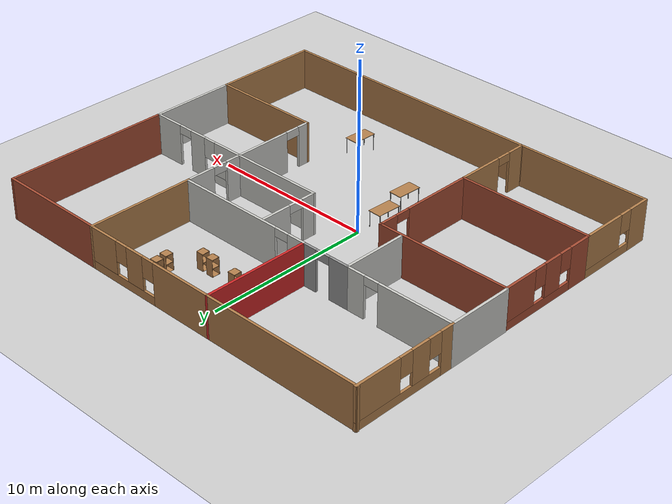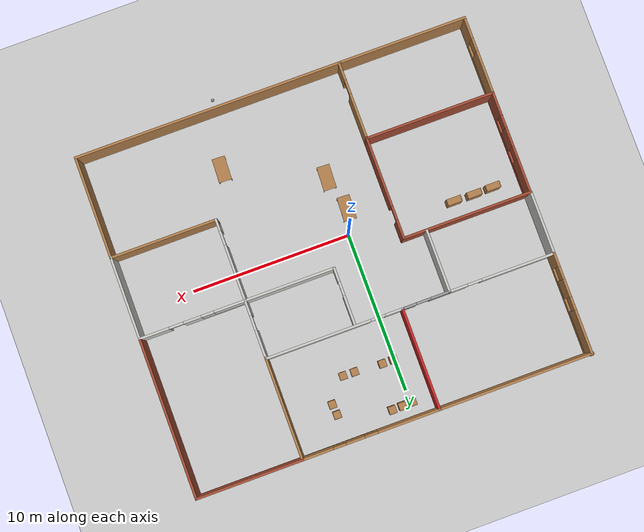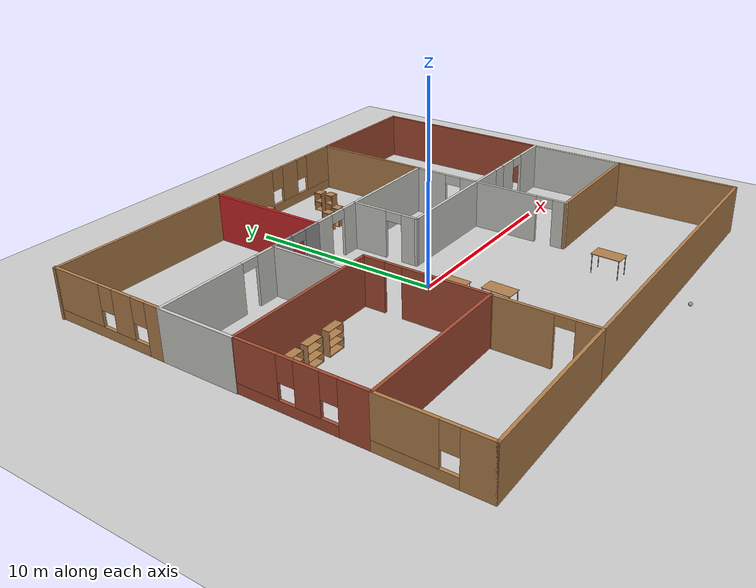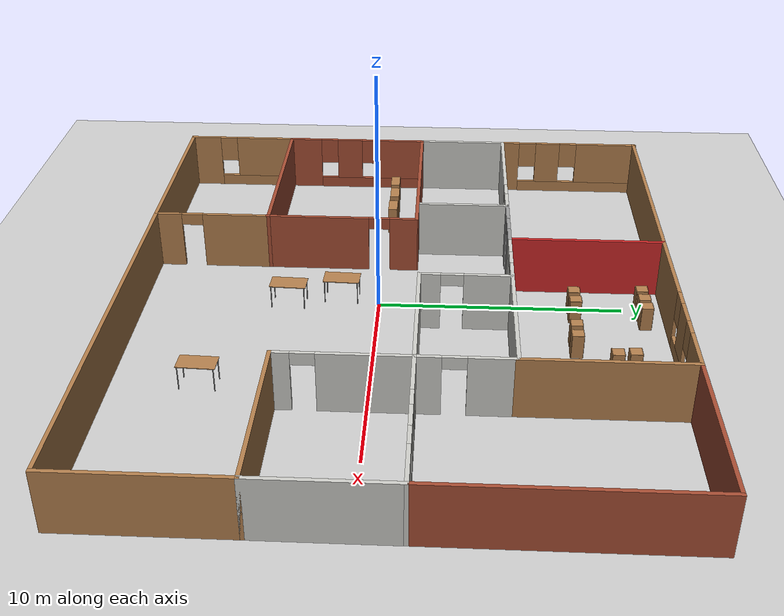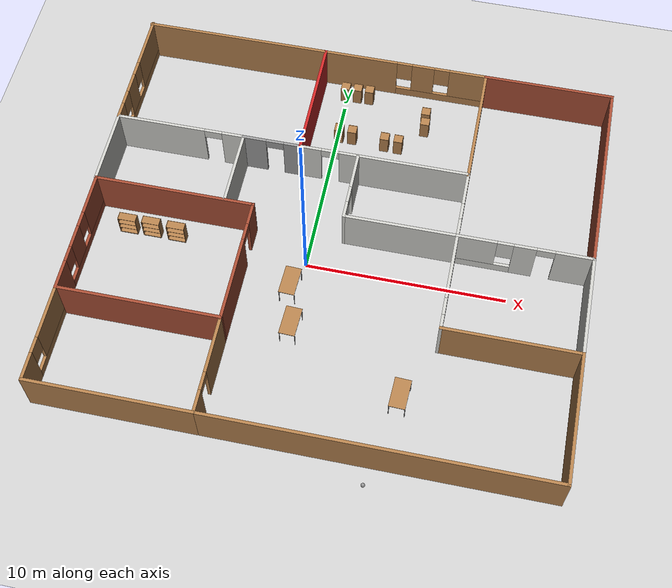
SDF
<sdf version="1.6">
 <world name="default">
  <light name="sun" type="directional">
   <pose>0 0 10 0 -0 0</pose>
   <diffuse>0.8 0.8 0.8 1</diffuse>
   <specular>0.2 0.2 0.2 1</specular>
   <attenuation>
    <range>1000</range>
    <constant>0.9</constant>
    <linear>0.01</linear>
    <quadratic>0.001</quadratic>
   </attenuation>
   <direction>-0.5 0.1 -0.9</direction>
  </light>
  <model name="ground_plane">
   <static>1</static>
   <link name="link">
    <collision name="collision">
     <geometry><plane><normal>0 0 1</normal><size>100 100</size></plane></geometry>
     <surface><friction><ode><mu>100</mu><mu2>50</mu2></ode></friction></surface>
    </collision>
    <visual name="visual">
     <cast_shadows>0</cast_shadows>
     <geometry><plane><normal>0 0 1</normal><size>100 100</size></plane></geometry>
     <material>
      <script><uri>file://media/materials/scripts/gazebo.material</uri><name>Gazebo/Grey</name></script>
     </material>
    </visual>
   </link>
  </model>
  <gravity>0 0 -9.8</gravity>
  <magnetic_field>6e-06 2.3e-05 -4.2e-05</magnetic_field>
  <atmosphere type="adiabatic"/>
  <physics name="default_physics" default="0" type="ode">
   <max_step_size>0.001</max_step_size>
   <real_time_factor>1</real_time_factor>
   <real_time_update_rate>1000</real_time_update_rate>
  </physics>
  <scene><ambient>0.4 0.4 0.4 1</ambient><background>0.7 0.7 0.7 1</background><shadows>1</shadows></scene>
  <spherical_coordinates>
   <surface_model>EARTH_WGS84</surface_model>
   <latitude_deg>0</latitude_deg>
   <longitude_deg>0</longitude_deg>
   <elevation>0</elevation>
   <heading_deg>0</heading_deg>
  </spherical_coordinates>
  <model name="building">
   <pose>1.3748 0.98314 0 0 -0 0</pose>
   <link name="Wall_102">
    <pose>5.78961 2.52674 0 0 -0 1.5708</pose>
    <visual name="Wall_102_Visual_0">
     <pose>-1.35652 0 1.25 0 -0 0</pose>
     <geometry><box><size>1.03697 0.15 2.5</size></box></geometry>
     <material>
      <script><uri>file://media/materials/scripts/gazebo.material</uri><name>Gazebo/CeilingTiled</name></script>
      <ambient>1 1 1 1</ambient>
     </material>
     <meta><layer>0</layer></meta>
    </visual>
    <collision name="Wall_102_Collision_0">
     <geometry><box><size>1.03697 0.15 2.5</size></box></geometry>
     <pose>-1.35652 0 1.25 0 -0 0</pose>
    </collision>
    <visual name="Wall_102_Visual_1">
     <pose>0.968484 0 1.25 0 -0 0</pose>
     <geometry><box><size>1.81303 0.15 2.5</size></box></geometry>
     <material>
      <script><uri>file://media/materials/scripts/gazebo.material</uri><name>Gazebo/CeilingTiled</name></script>
      <ambient>1 1 1 1</ambient>
     </material>
     <meta><layer>0</layer></meta>
    </visual>
    <collision name="Wall_102_Collision_1">
     <geometry><box><size>1.81303 0.15 2.5</size></box></geometry>
     <pose>0.968484 0 1.25 0 -0 0</pose>
    </collision>
    <visual name="Wall_102_Visual_2">
     <pose>-0.388033 0 2.25 0 -0 0</pose>
     <geometry><box><size>0.9 0.15 0.5</size></box></geometry>
     <material>
      <script><uri>file://media/materials/scripts/gazebo.material</uri><name>Gazebo/CeilingTiled</name></script>
      <ambient>1 1 1 1</ambient>
     </material>
     <meta><layer>0</layer></meta>
    </visual>
    <collision name="Wall_102_Collision_2">
     <geometry><box><size>0.9 0.15 0.5</size></box></geometry>
     <pose>-0.388033 0 2.25 0 -0 0</pose>
    </collision>
   </link>
   <link name="Wall_104">
    <collision name="Wall_104_Collision">
     <geometry><box><size>6.45348 0.15 2.5</size></box></geometry>
     <pose>0 0 1.25 0 -0 0</pose>
    </collision>
    <visual name="Wall_104_Visual">
     <pose>0 0 1.25 0 -0 0</pose>
     <geometry><box><size>6.45348 0.15 2.5</size></box></geometry>
     <material>
      <script><uri>file://media/materials/scripts/gazebo.material</uri><name>Gazebo/Red</name></script>
      <ambient>1 1 1 1</ambient>
     </material>
     <meta><layer>0</layer></meta>
    </visual>
    <pose>-2.78961 7.525 0 0 -0 1.5708</pose>
   </link>
   <link name="Wall_107">
    <collision name="Wall_107_Collision">
     <geometry><box><size>6.5 0.15 2.5</size></box></geometry>
     <pose>0 0 1.25 0 -0 0</pose>
    </collision>
    <visual name="Wall_107_Visual">
     <pose>0 0 1.25 0 -0 0</pose>
     <geometry><box><size>6.5 0.15 2.5</size></box></geometry>
     <material>
      <script><uri>file://media/materials/scripts/gazebo.material</uri><name>Gazebo/Wood</name></script>
      <ambient>1 1 1 1</ambient>
     </material>
     <meta><layer>0</layer></meta>
    </visual>
    <pose>5.78961 7.50174 0 0 -0 1.5708</pose>
   </link>
   <link name="Wall_111">
    <pose>-12.342 7.54826 0 0 -0 1.5708</pose>
    <visual name="Wall_111_Visual_0">
     <pose>-2.8028 0 1.25 0 -0 0</pose>
     <geometry><box><size>0.894393 0.15 2.5</size></box></geometry>
     <material>
      <script><uri>file://media/materials/scripts/gazebo.material</uri><name>Gazebo/Wood</name></script>
      <ambient>1 1 1 1</ambient>
     </material>
     <meta><layer>0</layer></meta>
    </visual>
    <collision name="Wall_111_Collision_0">
     <geometry><box><size>0.894393 0.15 2.5</size></box></geometry>
     <pose>-2.8028 0 1.25 0 -0 0</pose>
    </collision>
    <visual name="Wall_111_Visual_1">
     <pose>0.447197 0 0.25 0 -0 0</pose>
     <geometry><box><size>5.60561 0.15 0.5</size></box></geometry>
     <material>
      <script><uri>file://media/materials/scripts/gazebo.material</uri><name>Gazebo/Wood</name></script>
      <ambient>1 1 1 1</ambient>
     </material>
     <meta><layer>0</layer></meta>
    </visual>
    <collision name="Wall_111_Collision_1">
     <geometry><box><size>5.60561 0.15 0.5</size></box></geometry>
     <pose>0.447197 0 0.25 0 -0 0</pose>
    </collision>
    <visual name="Wall_111_Visual_2">
     <pose>-0.984121 0 1.5 0 -0 0</pose>
     <geometry><box><size>1.14297 0.15 2</size></box></geometry>
     <material>
      <script><uri>file://media/materials/scripts/gazebo.material</uri><name>Gazebo/Wood</name></script>
      <ambient>1 1 1 1</ambient>
     </material>
     <meta><layer>0</layer></meta>
    </visual>
    <collision name="Wall_111_Collision_2">
     <geometry><box><size>1.14297 0.15 2</size></box></geometry>
     <pose>-0.984121 0 1.5 0 -0 0</pose>
    </collision>
    <visual name="Wall_111_Visual_3">
     <pose>1.81868 0 1.5 0 -0 0</pose>
     <geometry><box><size>2.86264 0.15 2</size></box></geometry>
     <material>
      <script><uri>file://media/materials/scripts/gazebo.material</uri><name>Gazebo/Wood</name></script>
      <ambient>1 1 1 1</ambient>
     </material>
     <meta><layer>0</layer></meta>
    </visual>
    <collision name="Wall_111_Collision_3">
     <geometry><box><size>2.86264 0.15 2</size></box></geometry>
     <pose>1.81868 0 1.5 0 -0 0</pose>
    </collision>
    <visual name="Wall_111_Visual_4">
     <pose>-1.95561 0 1.9 0 -0 0</pose>
     <geometry><box><size>0.8 0.15 1.2</size></box></geometry>
     <material>
      <script><uri>file://media/materials/scripts/gazebo.material</uri><name>Gazebo/Wood</name></script>
      <ambient>1 1 1 1</ambient>
     </material>
     <meta><layer>0</layer></meta>
    </visual>
    <collision name="Wall_111_Collision_4">
     <geometry><box><size>0.8 0.15 1.2</size></box></geometry>
     <pose>-1.95561 0 1.9 0 -0 0</pose>
    </collision>
    <visual name="Wall_111_Visual_5">
     <pose>-0.012636 0 1.9 0 -0 0</pose>
     <geometry><box><size>0.8 0.15 1.2</size></box></geometry>
     <material>
      <script><uri>file://media/materials/scripts/gazebo.material</uri><name>Gazebo/Wood</name></script>
      <ambient>1 1 1 1</ambient>
     </material>
     <meta><layer>0</layer></meta>
    </visual>
    <collision name="Wall_111_Collision_5">
     <geometry><box><size>0.8 0.15 1.2</size></box></geometry>
     <pose>-0.012636 0 1.9 0 -0 0</pose>
    </collision>
   </link>
   <link name="Wall_115">
    <collision name="Wall_115_Collision">
     <geometry><box><size>9.75 0.15 2.5</size></box></geometry>
     <pose>0 0 1.25 0 -0 0</pose>
    </collision>
    <visual name="Wall_115_Visual">
     <pose>0 0 1.25 0 -0 0</pose>
     <geometry><box><size>9.75 0.15 2.5</size></box></geometry>
     <material>
      <script><uri>file://media/materials/scripts/gazebo.material</uri><name>Gazebo/Wood</name></script>
      <ambient>1 1 1 1</ambient>
     </material>
     <meta><layer>0</layer></meta>
    </visual>
    <pose>-7.58961 10.6767 0 0 -0 3.14159</pose>
   </link>
   <link name="Wall_118">
    <collision name="Wall_118_Collision">
     <geometry><box><size>6.75 0.15 2.5</size></box></geometry>
     <pose>0 0 1.25 0 -0 0</pose>
    </collision>
    <visual name="Wall_118_Visual">
     <pose>0 0 1.25 0 -0 0</pose>
     <geometry><box><size>6.75 0.15 2.5</size></box></geometry>
     <material>
      <script><uri>file://media/materials/scripts/gazebo.material</uri><name>Gazebo/Bricks</name></script>
      <ambient>1 1 1 1</ambient>
     </material>
     <meta><layer>0</layer></meta>
    </visual>
    <pose>9.08961 10.6767 0 0 -0 0</pose>
   </link>
   <link name="Wall_119">
    <collision name="Wall_119_Collision">
     <geometry><box><size>10 0.15 2.5</size></box></geometry>
     <pose>0 0 1.25 0 -0 0</pose>
    </collision>
    <visual name="Wall_119_Visual">
     <pose>0 0 1.25 0 -0 0</pose>
     <geometry><box><size>10 0.15 2.5</size></box></geometry>
     <material>
      <script><uri>file://media/materials/scripts/gazebo.material</uri><name>Gazebo/Bricks</name></script>
      <ambient>1 1 1 1</ambient>
     </material>
     <meta><layer>0</layer></meta>
    </visual>
    <pose>12.3896 5.75174 0 0 0 -1.5708</pose>
   </link>
   <link name="Wall_14">
    <collision name="Wall_14_Collision">
     <geometry><box><size>8.1171 0.15 2.5</size></box></geometry>
     <pose>0 0 1.25 0 -0 0</pose>
    </collision>
    <visual name="Wall_14_Visual">
     <pose>0 0 1.25 0 -0 0</pose>
     <geometry><box><size>8.1171 0.15 2.5</size></box></geometry>
     <material>
      <script><uri>file://media/materials/scripts/gazebo.material</uri><name>Gazebo/Wood</name></script>
      <ambient>1 1 1 1</ambient>
     </material>
     <meta><layer>0</layer></meta>
    </visual>
    <pose>-8.32684 -10.7233 0 0 -0 0</pose>
   </link>
   <link name="Wall_16">
    <pose>-4.29676 -8.29826 0 0 -0 1.5708</pose>
    <visual name="Wall_16_Visual_0">
     <pose>-1.90821 0 1.25 0 -0 0</pose>
     <geometry><box><size>1.18359 0.15 2.5</size></box></geometry>
     <material>
      <script><uri>file://media/materials/scripts/gazebo.material</uri><name>Gazebo/Wood</name></script>
      <ambient>1 1 1 1</ambient>
     </material>
     <meta><layer>0</layer></meta>
    </visual>
    <collision name="Wall_16_Collision_0">
     <geometry><box><size>1.18359 0.15 2.5</size></box></geometry>
     <pose>-1.90821 0 1.25 0 -0 0</pose>
    </collision>
    <visual name="Wall_16_Visual_1">
     <pose>1.04179 0 1.25 0 -0 0</pose>
     <geometry><box><size>2.91641 0.15 2.5</size></box></geometry>
     <material>
      <script><uri>file://media/materials/scripts/gazebo.material</uri><name>Gazebo/Wood</name></script>
      <ambient>1 1 1 1</ambient>
     </material>
     <meta><layer>0</layer></meta>
    </visual>
    <collision name="Wall_16_Collision_1">
     <geometry><box><size>2.91641 0.15 2.5</size></box></geometry>
     <pose>1.04179 0 1.25 0 -0 0</pose>
    </collision>
    <visual name="Wall_16_Visual_2">
     <pose>-0.866411 0 2.25 0 -0 0</pose>
     <geometry><box><size>0.9 0.15 0.5</size></box></geometry>
     <material>
      <script><uri>file://media/materials/scripts/gazebo.material</uri><name>Gazebo/Wood</name></script>
      <ambient>1 1 1 1</ambient>
     </material>
     <meta><layer>0</layer></meta>
    </visual>
    <collision name="Wall_16_Collision_2">
     <geometry><box><size>0.9 0.15 0.5</size></box></geometry>
     <pose>-0.866411 0 2.25 0 -0 0</pose>
    </collision>
   </link>
   <link name="Wall_20">
    <pose>-12.3104 -8.29826 0 0 -0 1.5708</pose>
    <visual name="Wall_20_Visual_0">
     <pose>-1.79068 0 1.25 0 -0 0</pose>
     <geometry><box><size>1.41863 0.15 2.5</size></box></geometry>
     <material>
      <script><uri>file://media/materials/scripts/gazebo.material</uri><name>Gazebo/Wood</name></script>
      <ambient>1 1 1 1</ambient>
     </material>
     <meta><layer>0</layer></meta>
    </visual>
    <collision name="Wall_20_Collision_0">
     <geometry><box><size>1.41863 0.15 2.5</size></box></geometry>
     <pose>-1.79068 0 1.25 0 -0 0</pose>
    </collision>
    <visual name="Wall_20_Visual_1">
     <pose>0.709317 0 0.25 0 -0 0</pose>
     <geometry><box><size>3.58137 0.15 0.5</size></box></geometry>
     <material>
      <script><uri>file://media/materials/scripts/gazebo.material</uri><name>Gazebo/Wood</name></script>
      <ambient>1 1 1 1</ambient>
     </material>
     <meta><layer>0</layer></meta>
    </visual>
    <collision name="Wall_20_Collision_1">
     <geometry><box><size>3.58137 0.15 0.5</size></box></geometry>
     <pose>0.709317 0 0.25 0 -0 0</pose>
    </collision>
    <visual name="Wall_20_Visual_2">
     <pose>1.10932 0 1.5 0 -0 0</pose>
     <geometry><box><size>2.78137 0.15 2</size></box></geometry>
     <material>
      <script><uri>file://media/materials/scripts/gazebo.material</uri><name>Gazebo/Wood</name></script>
      <ambient>1 1 1 1</ambient>
     </material>
     <meta><layer>0</layer></meta>
    </visual>
    <collision name="Wall_20_Collision_2">
     <geometry><box><size>2.78137 0.15 2</size></box></geometry>
     <pose>1.10932 0 1.5 0 -0 0</pose>
    </collision>
    <visual name="Wall_20_Visual_3">
     <pose>-0.681367 0 1.9 0 -0 0</pose>
     <geometry><box><size>0.8 0.15 1.2</size></box></geometry>
     <material>
      <script><uri>file://media/materials/scripts/gazebo.material</uri><name>Gazebo/Wood</name></script>
      <ambient>1 1 1 1</ambient>
     </material>
     <meta><layer>0</layer></meta>
    </visual>
    <collision name="Wall_20_Collision_3">
     <geometry><box><size>0.8 0.15 1.2</size></box></geometry>
     <pose>-0.681367 0 1.9 0 -0 0</pose>
    </collision>
   </link>
   <link name="Wall_22">
    <collision name="Wall_22_Collision">
     <geometry><box><size>8.16363 0.15 2.5</size></box></geometry>
     <pose>0 0 1.25 0 -0 0</pose>
    </collision>
    <visual name="Wall_22_Visual">
     <pose>0 0 1.25 0 -0 0</pose>
     <geometry><box><size>8.16363 0.15 2.5</size></box></geometry>
     <material>
      <script><uri>file://media/materials/scripts/gazebo.material</uri><name>Gazebo/Bricks</name></script>
      <ambient>1 1 1 1</ambient>
     </material>
     <meta><layer>0</layer></meta>
    </visual>
    <pose>-8.30358 -5.87326 0 0 -0 0</pose>
   </link>
   <link name="Wall_24">
    <collision name="Wall_24_Collision">
     <geometry><box><size>16.8829 0.15 2.5</size></box></geometry>
     <pose>0 0 1.25 0 -0 0</pose>
    </collision>
    <visual name="Wall_24_Visual">
     <pose>0 0 1.25 0 -0 0</pose>
     <geometry><box><size>16.8829 0.15 2.5</size></box></geometry>
     <material>
      <script><uri>file://media/materials/scripts/gazebo.material</uri><name>Gazebo/Wood</name></script>
      <ambient>1 1 1 1</ambient>
     </material>
     <meta><layer>0</layer></meta>
    </visual>
    <pose>4.02316 -10.7233 0 0 -0 0</pose>
   </link>
   <link name="Wall_26">
    <collision name="Wall_26_Collision">
     <geometry><box><size>6.5 0.15 2.5</size></box></geometry>
     <pose>0 0 1.25 0 -0 0</pose>
    </collision>
    <visual name="Wall_26_Visual">
     <pose>0 0 1.25 0 -0 0</pose>
     <geometry><box><size>6.5 0.15 2.5</size></box></geometry>
     <material>
      <script><uri>file://media/materials/scripts/gazebo.material</uri><name>Gazebo/Wood</name></script>
      <ambient>1 1 1 1</ambient>
     </material>
     <meta><layer>0</layer></meta>
    </visual>
    <pose>12.3896 -7.54826 0 0 -0 1.5708</pose>
   </link>
   <link name="Wall_27">
    <collision name="Wall_27_Collision">
     <geometry><box><size>6.75 0.15 2.5</size></box></geometry>
     <pose>0 0 1.25 0 -0 0</pose>
    </collision>
    <visual name="Wall_27_Visual">
     <pose>0 0 1.25 0 -0 0</pose>
     <geometry><box><size>6.75 0.15 2.5</size></box></geometry>
     <material>
      <script><uri>file://media/materials/scripts/gazebo.material</uri><name>Gazebo/Wood</name></script>
      <ambient>1 1 1 1</ambient>
     </material>
     <meta><layer>0</layer></meta>
    </visual>
    <pose>9.08961 -4.37326 0 0 -0 3.14159</pose>
   </link>
   <link name="Wall_33">
    <pose>-12.3104 -2.69826 0 0 -0 1.5708</pose>
    <visual name="Wall_33_Visual_0">
     <pose>-2.49071 0 1.25 0 -0 0</pose>
     <geometry><box><size>1.51858 0.15 2.5</size></box></geometry>
     <material>
      <script><uri>file://media/materials/scripts/gazebo.material</uri><name>Gazebo/Bricks</name></script>
      <ambient>1 1 1 1</ambient>
     </material>
     <meta><layer>0</layer></meta>
    </visual>
    <collision name="Wall_33_Collision_0">
     <geometry><box><size>1.51858 0.15 2.5</size></box></geometry>
     <pose>-2.49071 0 1.25 0 -0 0</pose>
    </collision>
    <visual name="Wall_33_Visual_1">
     <pose>0.759292 0 0.25 0 -0 0</pose>
     <geometry><box><size>4.98142 0.15 0.5</size></box></geometry>
     <material>
      <script><uri>file://media/materials/scripts/gazebo.material</uri><name>Gazebo/Bricks</name></script>
      <ambient>1 1 1 1</ambient>
     </material>
     <meta><layer>0</layer></meta>
    </visual>
    <collision name="Wall_33_Collision_1">
     <geometry><box><size>4.98142 0.15 0.5</size></box></geometry>
     <pose>0.759292 0 0.25 0 -0 0</pose>
    </collision>
    <visual name="Wall_33_Visual_2">
     <pose>-0.3368 0 1.5 0 -0 0</pose>
     <geometry><box><size>1.18923 0.15 2</size></box></geometry>
     <material>
      <script><uri>file://media/materials/scripts/gazebo.material</uri><name>Gazebo/Bricks</name></script>
      <ambient>1 1 1 1</ambient>
     </material>
     <meta><layer>0</layer></meta>
    </visual>
    <collision name="Wall_33_Collision_2">
     <geometry><box><size>1.18923 0.15 2</size></box></geometry>
     <pose>-0.3368 0 1.5 0 -0 0</pose>
    </collision>
    <visual name="Wall_33_Visual_3">
     <pose>2.15391 0 1.5 0 -0 0</pose>
     <geometry><box><size>2.19218 0.15 2</size></box></geometry>
     <material>
      <script><uri>file://media/materials/scripts/gazebo.material</uri><name>Gazebo/Bricks</name></script>
      <ambient>1 1 1 1</ambient>
     </material>
     <meta><layer>0</layer></meta>
    </visual>
    <collision name="Wall_33_Collision_3">
     <geometry><box><size>2.19218 0.15 2</size></box></geometry>
     <pose>2.15391 0 1.5 0 -0 0</pose>
    </collision>
    <visual name="Wall_33_Visual_4">
     <pose>-1.33142 0 1.9 0 -0 0</pose>
     <geometry><box><size>0.8 0.15 1.2</size></box></geometry>
     <material>
      <script><uri>file://media/materials/scripts/gazebo.material</uri><name>Gazebo/Bricks</name></script>
      <ambient>1 1 1 1</ambient>
     </material>
     <meta><layer>0</layer></meta>
    </visual>
    <collision name="Wall_33_Collision_4">
     <geometry><box><size>0.8 0.15 1.2</size></box></geometry>
     <pose>-1.33142 0 1.9 0 -0 0</pose>
    </collision>
    <visual name="Wall_33_Visual_5">
     <pose>0.657816 0 1.9 0 -0 0</pose>
     <geometry><box><size>0.8 0.15 1.2</size></box></geometry>
     <material>
      <script><uri>file://media/materials/scripts/gazebo.material</uri><name>Gazebo/Bricks</name></script>
      <ambient>1 1 1 1</ambient>
     </material>
     <meta><layer>0</layer></meta>
    </visual>
    <collision name="Wall_33_Collision_5">
     <geometry><box><size>0.8 0.15 1.2</size></box></geometry>
     <pose>0.657816 0 1.9 0 -0 0</pose>
    </collision>
   </link>
   <link name="Wall_34">
    <collision name="Wall_34_Collision">
     <geometry><box><size>8.16363 0.15 2.5</size></box></geometry>
     <pose>0 0 1.25 0 -0 0</pose>
    </collision>
    <visual name="Wall_34_Visual">
     <pose>0 0 1.25 0 -0 0</pose>
     <geometry><box><size>8.16363 0.15 2.5</size></box></geometry>
     <material>
      <script><uri>file://media/materials/scripts/gazebo.material</uri><name>Gazebo/Bricks</name></script>
      <ambient>1 1 1 1</ambient>
     </material>
     <meta><layer>0</layer></meta>
    </visual>
    <pose>-8.30358 0.476738 0 0 -0 0</pose>
   </link>
   <link name="Wall_35">
    <pose>-4.29676 -2.74479 0 0 0 -1.5708</pose>
    <visual name="Wall_35_Visual_0">
     <pose>-2.66441 0 1.25 0 -0 0</pose>
     <geometry><box><size>1.17118 0.15 2.5</size></box></geometry>
     <material>
      <script><uri>file://media/materials/scripts/gazebo.material</uri><name>Gazebo/Bricks</name></script>
      <ambient>1 1 1 1</ambient>
     </material>
     <meta><layer>0</layer></meta>
    </visual>
    <collision name="Wall_35_Collision_0">
     <geometry><box><size>1.17118 0.15 2.5</size></box></geometry>
     <pose>-2.66441 0 1.25 0 -0 0</pose>
    </collision>
    <visual name="Wall_35_Visual_1">
     <pose>1.03559 0 1.25 0 -0 0</pose>
     <geometry><box><size>4.42882 0.15 2.5</size></box></geometry>
     <material>
      <script><uri>file://media/materials/scripts/gazebo.material</uri><name>Gazebo/Bricks</name></script>
      <ambient>1 1 1 1</ambient>
     </material>
     <meta><layer>0</layer></meta>
    </visual>
    <collision name="Wall_35_Collision_1">
     <geometry><box><size>4.42882 0.15 2.5</size></box></geometry>
     <pose>1.03559 0 1.25 0 -0 0</pose>
    </collision>
    <visual name="Wall_35_Visual_2">
     <pose>-1.62882 0 2.25 0 -0 0</pose>
     <geometry><box><size>0.9 0.15 0.5</size></box></geometry>
     <material>
      <script><uri>file://media/materials/scripts/gazebo.material</uri><name>Gazebo/Bricks</name></script>
      <ambient>1 1 1 1</ambient>
     </material>
     <meta><layer>0</layer></meta>
    </visual>
    <collision name="Wall_35_Collision_2">
     <geometry><box><size>0.9 0.15 0.5</size></box></geometry>
     <pose>-1.62882 0 2.25 0 -0 0</pose>
    </collision>
   </link>
   <link name="Wall_69">
    <pose>1.46157 10.6767 0 0 -0 0</pose>
    <visual name="Wall_69_Visual_0">
     <pose>-2.34247 0 1.25 0 -0 0</pose>
     <geometry><box><size>3.92114 0.15 2.5</size></box></geometry>
     <material>
      <script><uri>file://media/materials/scripts/gazebo.material</uri><name>Gazebo/Wood</name></script>
      <ambient>1 1 1 1</ambient>
     </material>
     <meta><layer>0</layer></meta>
    </visual>
    <collision name="Wall_69_Collision_0">
     <geometry><box><size>3.92114 0.15 2.5</size></box></geometry>
     <pose>-2.34247 0 1.25 0 -0 0</pose>
    </collision>
    <visual name="Wall_69_Visual_1">
     <pose>1.96057 0 0.25 0 -0 0</pose>
     <geometry><box><size>4.68495 0.15 0.5</size></box></geometry>
     <material>
      <script><uri>file://media/materials/scripts/gazebo.material</uri><name>Gazebo/Wood</name></script>
      <ambient>1 1 1 1</ambient>
     </material>
     <meta><layer>0</layer></meta>
    </visual>
    <collision name="Wall_69_Collision_1">
     <geometry><box><size>4.68495 0.15 0.5</size></box></geometry>
     <pose>1.96057 0 0.25 0 -0 0</pose>
    </collision>
    <visual name="Wall_69_Visual_2">
     <pose>1.01271 0 1.5 0 -0 0</pose>
     <geometry><box><size>1.18923 0.15 2</size></box></geometry>
     <material>
      <script><uri>file://media/materials/scripts/gazebo.material</uri><name>Gazebo/Wood</name></script>
      <ambient>1 1 1 1</ambient>
     </material>
     <meta><layer>0</layer></meta>
    </visual>
    <collision name="Wall_69_Collision_2">
     <geometry><box><size>1.18923 0.15 2</size></box></geometry>
     <pose>1.01271 0 1.5 0 -0 0</pose>
    </collision>
    <visual name="Wall_69_Visual_3">
     <pose>3.35519 0 1.5 0 -0 0</pose>
     <geometry><box><size>1.89572 0.15 2</size></box></geometry>
     <material>
      <script><uri>file://media/materials/scripts/gazebo.material</uri><name>Gazebo/Wood</name></script>
      <ambient>1 1 1 1</ambient>
     </material>
     <meta><layer>0</layer></meta>
    </visual>
    <collision name="Wall_69_Collision_3">
     <geometry><box><size>1.89572 0.15 2</size></box></geometry>
     <pose>3.35519 0 1.5 0 -0 0</pose>
    </collision>
    <visual name="Wall_69_Visual_4">
     <pose>0.018094 0 1.9 0 -0 0</pose>
     <geometry><box><size>0.8 0.15 1.2</size></box></geometry>
     <material>
      <script><uri>file://media/materials/scripts/gazebo.material</uri><name>Gazebo/Wood</name></script>
      <ambient>1 1 1 1</ambient>
     </material>
     <meta><layer>0</layer></meta>
    </visual>
    <collision name="Wall_69_Collision_4">
     <geometry><box><size>0.8 0.15 1.2</size></box></geometry>
     <pose>0.018094 0 1.9 0 -0 0</pose>
    </collision>
    <visual name="Wall_69_Visual_5">
     <pose>2.00733 0 1.9 0 -0 0</pose>
     <geometry><box><size>0.8 0.15 1.2</size></box></geometry>
     <material>
      <script><uri>file://media/materials/scripts/gazebo.material</uri><name>Gazebo/Wood</name></script>
      <ambient>1 1 1 1</ambient>
     </material>
     <meta><layer>0</layer></meta>
    </visual>
    <collision name="Wall_69_Collision_5">
     <geometry><box><size>0.8 0.15 1.2</size></box></geometry>
     <pose>2.00733 0 1.9 0 -0 0</pose>
    </collision>
   </link>
   <link name="Wall_72">
    <collision name="Wall_72_Collision">
     <geometry><box><size>5.25 0.15 2.5</size></box></geometry>
     <pose>0 0 1.25 0 -0 0</pose>
    </collision>
    <visual name="Wall_72_Visual">
     <pose>0 0 1.25 0 -0 0</pose>
     <geometry><box><size>5.25 0.15 2.5</size></box></geometry>
     <material>
      <script><uri>file://media/materials/scripts/gazebo.material</uri><name>Gazebo/CeilingTiled</name></script>
      <ambient>1 1 1 1</ambient>
     </material>
     <meta><layer>0</layer></meta>
    </visual>
    <pose>12.3896 -1.82326 0 0 -0 1.5708</pose>
   </link>
   <link name="Wall_75">
    <pose>5.78961 -1.82326 0 0 -0 1.5708</pose>
    <visual name="Wall_75_Visual_0">
     <pose>-2.23326 0 1.25 0 -0 0</pose>
     <geometry><box><size>0.783487 0.15 2.5</size></box></geometry>
     <material>
      <script><uri>file://media/materials/scripts/gazebo.material</uri><name>Gazebo/CeilingTiled</name></script>
      <ambient>1 1 1 1</ambient>
     </material>
     <meta><layer>0</layer></meta>
    </visual>
    <collision name="Wall_75_Collision_0">
     <geometry><box><size>0.783487 0.15 2.5</size></box></geometry>
     <pose>-2.23326 0 1.25 0 -0 0</pose>
    </collision>
    <visual name="Wall_75_Visual_1">
     <pose>0.841744 0 1.25 0 -0 0</pose>
     <geometry><box><size>3.56651 0.15 2.5</size></box></geometry>
     <material>
      <script><uri>file://media/materials/scripts/gazebo.material</uri><name>Gazebo/CeilingTiled</name></script>
      <ambient>1 1 1 1</ambient>
     </material>
     <meta><layer>0</layer></meta>
    </visual>
    <collision name="Wall_75_Collision_1">
     <geometry><box><size>3.56651 0.15 2.5</size></box></geometry>
     <pose>0.841744 0 1.25 0 -0 0</pose>
    </collision>
    <visual name="Wall_75_Visual_2">
     <pose>-1.39151 0 2.25 0 -0 0</pose>
     <geometry><box><size>0.9 0.15 0.5</size></box></geometry>
     <material>
      <script><uri>file://media/materials/scripts/gazebo.material</uri><name>Gazebo/CeilingTiled</name></script>
      <ambient>1 1 1 1</ambient>
     </material>
     <meta><layer>0</layer></meta>
    </visual>
    <collision name="Wall_75_Collision_2">
     <geometry><box><size>0.9 0.15 0.5</size></box></geometry>
     <pose>-1.39151 0 2.25 0 -0 0</pose>
    </collision>
   </link>
   <link name="Wall_77">
    <pose>9.08961 0.726738 0 0 -0 3.14159</pose>
    <visual name="Wall_77_Visual_0">
     <pose>-2.4187 0 1.25 0 -0 0</pose>
     <geometry><box><size>1.91261 0.15 2.5</size></box></geometry>
     <material>
      <script><uri>file://media/materials/scripts/gazebo.material</uri><name>Gazebo/CeilingTiled</name></script>
      <ambient>1 1 1 1</ambient>
     </material>
     <meta><layer>0</layer></meta>
    </visual>
    <collision name="Wall_77_Collision_0">
     <geometry><box><size>1.91261 0.15 2.5</size></box></geometry>
     <pose>-2.4187 0 1.25 0 -0 0</pose>
    </collision>
    <visual name="Wall_77_Visual_1">
     <pose>-0.007028 0 1.25 0 -0 0</pose>
     <geometry><box><size>1.11073 0.15 2.5</size></box></geometry>
     <material>
      <script><uri>file://media/materials/scripts/gazebo.material</uri><name>Gazebo/CeilingTiled</name></script>
      <ambient>1 1 1 1</ambient>
     </material>
     <meta><layer>0</layer></meta>
    </visual>
    <collision name="Wall_77_Collision_1">
     <geometry><box><size>1.11073 0.15 2.5</size></box></geometry>
     <pose>-0.007028 0 1.25 0 -0 0</pose>
    </collision>
    <visual name="Wall_77_Visual_2">
     <pose>1.96167 0 0.25 0 -0 0</pose>
     <geometry><box><size>2.82666 0.15 0.5</size></box></geometry>
     <material>
      <script><uri>file://media/materials/scripts/gazebo.material</uri><name>Gazebo/CeilingTiled</name></script>
      <ambient>1 1 1 1</ambient>
     </material>
     <meta><layer>0</layer></meta>
    </visual>
    <collision name="Wall_77_Collision_2">
     <geometry><box><size>2.82666 0.15 0.5</size></box></geometry>
     <pose>1.96167 0 0.25 0 -0 0</pose>
    </collision>
    <visual name="Wall_77_Visual_3">
     <pose>2.36167 0 1.5 0 -0 0</pose>
     <geometry><box><size>2.02666 0.15 2</size></box></geometry>
     <material>
      <script><uri>file://media/materials/scripts/gazebo.material</uri><name>Gazebo/CeilingTiled</name></script>
      <ambient>1 1 1 1</ambient>
     </material>
     <meta><layer>0</layer></meta>
    </visual>
    <collision name="Wall_77_Collision_3">
     <geometry><box><size>2.02666 0.15 2</size></box></geometry>
     <pose>2.36167 0 1.5 0 -0 0</pose>
    </collision>
    <visual name="Wall_77_Visual_4">
     <pose>0.948336 0 1.9 0 -0 0</pose>
     <geometry><box><size>0.8 0.15 1.2</size></box></geometry>
     <material>
      <script><uri>file://media/materials/scripts/gazebo.material</uri><name>Gazebo/CeilingTiled</name></script>
      <ambient>1 1 1 1</ambient>
     </material>
     <meta><layer>0</layer></meta>
    </visual>
    <collision name="Wall_77_Collision_4">
     <geometry><box><size>0.8 0.15 1.2</size></box></geometry>
     <pose>0.948336 0 1.9 0 -0 0</pose>
    </collision>
    <visual name="Wall_77_Visual_5">
     <pose>-1.01239 0 2.25 0 -0 0</pose>
     <geometry><box><size>0.9 0.15 0.5</size></box></geometry>
     <material>
      <script><uri>file://media/materials/scripts/gazebo.material</uri><name>Gazebo/CeilingTiled</name></script>
      <ambient>1 1 1 1</ambient>
     </material>
     <meta><layer>0</layer></meta>
    </visual>
    <collision name="Wall_77_Collision_5">
     <geometry><box><size>0.9 0.15 0.5</size></box></geometry>
     <pose>-1.01239 0 2.25 0 -0 0</pose>
    </collision>
   </link>
   <link name="Wall_83">
    <pose>1.47078 4.37326 0 0 -0 0</pose>
    <visual name="Wall_83_Visual_0">
     <pose>-3.73839 0 1.25 0 -0 0</pose>
     <geometry><box><size>1.14775 0.15 2.5</size></box></geometry>
     <material>
      <script><uri>file://media/materials/scripts/gazebo.material</uri><name>Gazebo/CeilingTiled</name></script>
      <ambient>1 1 1 1</ambient>
     </material>
     <meta><layer>0</layer></meta>
    </visual>
    <collision name="Wall_83_Collision_0">
     <geometry><box><size>1.14775 0.15 2.5</size></box></geometry>
     <pose>-3.73839 0 1.25 0 -0 0</pose>
    </collision>
    <visual name="Wall_83_Visual_1">
     <pose>1.02388 0 1.25 0 -0 0</pose>
     <geometry><box><size>6.57677 0.15 2.5</size></box></geometry>
     <material>
      <script><uri>file://media/materials/scripts/gazebo.material</uri><name>Gazebo/CeilingTiled</name></script>
      <ambient>1 1 1 1</ambient>
     </material>
     <meta><layer>0</layer></meta>
    </visual>
    <collision name="Wall_83_Collision_1">
     <geometry><box><size>6.57677 0.15 2.5</size></box></geometry>
     <pose>1.02388 0 1.25 0 -0 0</pose>
    </collision>
    <visual name="Wall_83_Visual_2">
     <pose>-2.71451 0 2.25 0 -0 0</pose>
     <geometry><box><size>0.9 0.15 0.5</size></box></geometry>
     <material>
      <script><uri>file://media/materials/scripts/gazebo.material</uri><name>Gazebo/CeilingTiled</name></script>
      <ambient>1 1 1 1</ambient>
     </material>
     <meta><layer>0</layer></meta>
    </visual>
    <collision name="Wall_83_Collision_2">
     <geometry><box><size>0.9 0.15 0.5</size></box></geometry>
     <pose>-2.71451 0 2.25 0 -0 0</pose>
    </collision>
   </link>
   <link name="Wall_85">
    <collision name="Wall_85_Collision">
     <geometry><box><size>5.75 0.15 2.5</size></box></geometry>
     <pose>0 0 1.25 0 -0 0</pose>
    </collision>
    <visual name="Wall_85_Visual">
     <pose>0 0 1.25 0 -0 0</pose>
     <geometry><box><size>5.75 0.15 2.5</size></box></geometry>
     <material>
      <script><uri>file://media/materials/scripts/gazebo.material</uri><name>Gazebo/CeilingTiled</name></script>
      <ambient>1 1 1 1</ambient>
     </material>
     <meta><layer>0</layer></meta>
    </visual>
    <pose>2.98961 0.726738 0 0 -0 3.14159</pose>
   </link>
   <link name="Wall_88">
    <pose>0.189609 2.52674 0 0 -0 1.5708</pose>
    <visual name="Wall_88_Visual_0">
     <pose>-1.41735 0 1.25 0 -0 0</pose>
     <geometry><box><size>0.915297 0.15 2.5</size></box></geometry>
     <material>
      <script><uri>file://media/materials/scripts/gazebo.material</uri><name>Gazebo/CeilingTiled</name></script>
      <ambient>1 1 1 1</ambient>
     </material>
     <meta><layer>0</layer></meta>
    </visual>
    <collision name="Wall_88_Collision_0">
     <geometry><box><size>0.915297 0.15 2.5</size></box></geometry>
     <pose>-1.41735 0 1.25 0 -0 0</pose>
    </collision>
    <visual name="Wall_88_Visual_1">
     <pose>0.907649 0 1.25 0 -0 0</pose>
     <geometry><box><size>1.9347 0.15 2.5</size></box></geometry>
     <material>
      <script><uri>file://media/materials/scripts/gazebo.material</uri><name>Gazebo/CeilingTiled</name></script>
      <ambient>1 1 1 1</ambient>
     </material>
     <meta><layer>0</layer></meta>
    </visual>
    <collision name="Wall_88_Collision_1">
     <geometry><box><size>1.9347 0.15 2.5</size></box></geometry>
     <pose>0.907649 0 1.25 0 -0 0</pose>
    </collision>
    <visual name="Wall_88_Visual_2">
     <pose>-0.509703 0 2.25 0 -0 0</pose>
     <geometry><box><size>0.9 0.15 0.5</size></box></geometry>
     <material>
      <script><uri>file://media/materials/scripts/gazebo.material</uri><name>Gazebo/CeilingTiled</name></script>
      <ambient>1 1 1 1</ambient>
     </material>
     <meta><layer>0</layer></meta>
    </visual>
    <collision name="Wall_88_Collision_2">
     <geometry><box><size>0.9 0.15 0.5</size></box></geometry>
     <pose>-0.509703 0 2.25 0 -0 0</pose>
    </collision>
   </link>
   <link name="Wall_90">
    <pose>-4.25422 4.37326 0 0 -0 3.14159</pose>
    <visual name="Wall_90_Visual_0">
     <pose>-1.08199 0 1.25 0 -0 0</pose>
     <geometry><box><size>0.961491 0.15 2.5</size></box></geometry>
     <material>
      <script><uri>file://media/materials/scripts/gazebo.material</uri><name>Gazebo/Grey</name></script>
      <ambient>1 1 1 1</ambient>
     </material>
     <meta><layer>0</layer></meta>
    </visual>
    <collision name="Wall_90_Collision_0">
     <geometry><box><size>0.961491 0.15 2.5</size></box></geometry>
     <pose>-1.08199 0 1.25 0 -0 0</pose>
    </collision>
    <visual name="Wall_90_Visual_1">
     <pose>0.930745 0 1.25 0 -0 0</pose>
     <geometry><box><size>1.26398 0.15 2.5</size></box></geometry>
     <material>
      <script><uri>file://media/materials/scripts/gazebo.material</uri><name>Gazebo/Grey</name></script>
      <ambient>1 1 1 1</ambient>
     </material>
     <meta><layer>0</layer></meta>
    </visual>
    <collision name="Wall_90_Collision_1">
     <geometry><box><size>1.26398 0.15 2.5</size></box></geometry>
     <pose>0.930745 0 1.25 0 -0 0</pose>
    </collision>
    <visual name="Wall_90_Visual_2">
     <pose>-0.151246 0 2.25 0 -0 0</pose>
     <geometry><box><size>0.9 0.15 0.5</size></box></geometry>
     <material>
      <script><uri>file://media/materials/scripts/gazebo.material</uri><name>Gazebo/Grey</name></script>
      <ambient>1 1 1 1</ambient>
     </material>
     <meta><layer>0</layer></meta>
    </visual>
    <collision name="Wall_90_Collision_2">
     <geometry><box><size>0.9 0.15 0.5</size></box></geometry>
     <pose>-0.151246 0 2.25 0 -0 0</pose>
    </collision>
   </link>
   <link name="Wall_93">
    <collision name="Wall_93_Collision">
     <geometry><box><size>4 0.15 2.5</size></box></geometry>
     <pose>0 0 1.25 0 -0 0</pose>
    </collision>
    <visual name="Wall_93_Visual">
     <pose>0 0 1.25 0 -0 0</pose>
     <geometry><box><size>4 0.15 2.5</size></box></geometry>
     <material>
      <script><uri>file://media/materials/scripts/gazebo.material</uri><name>Gazebo/CeilingTiled</name></script>
      <ambient>1 1 1 1</ambient>
     </material>
     <meta><layer>0</layer></meta>
    </visual>
    <pose>-5.74195 2.44826 0 0 0 -1.5708</pose>
   </link>
   <link name="Wall_95">
    <pose>-9.04195 4.37326 0 0 -0 3.14159</pose>
    <visual name="Wall_95_Visual_0">
     <pose>-2.76986 0 1.25 0 -0 0</pose>
     <geometry><box><size>1.21027 0.15 2.5</size></box></geometry>
     <material>
      <script><uri>file://media/materials/scripts/gazebo.material</uri><name>Gazebo/CeilingTiled</name></script>
      <ambient>1 1 1 1</ambient>
     </material>
     <meta><layer>0</layer></meta>
    </visual>
    <collision name="Wall_95_Collision_0">
     <geometry><box><size>1.21027 0.15 2.5</size></box></geometry>
     <pose>-2.76986 0 1.25 0 -0 0</pose>
    </collision>
    <visual name="Wall_95_Visual_1">
     <pose>1.05514 0 1.25 0 -0 0</pose>
     <geometry><box><size>4.63973 0.15 2.5</size></box></geometry>
     <material>
      <script><uri>file://media/materials/scripts/gazebo.material</uri><name>Gazebo/CeilingTiled</name></script>
      <ambient>1 1 1 1</ambient>
     </material>
     <meta><layer>0</layer></meta>
    </visual>
    <collision name="Wall_95_Collision_1">
     <geometry><box><size>4.63973 0.15 2.5</size></box></geometry>
     <pose>1.05514 0 1.25 0 -0 0</pose>
    </collision>
    <visual name="Wall_95_Visual_2">
     <pose>-1.71473 0 2.25 0 -0 0</pose>
     <geometry><box><size>0.9 0.15 0.5</size></box></geometry>
     <material>
      <script><uri>file://media/materials/scripts/gazebo.material</uri><name>Gazebo/CeilingTiled</name></script>
      <ambient>1 1 1 1</ambient>
     </material>
     <meta><layer>0</layer></meta>
    </visual>
    <collision name="Wall_95_Collision_2">
     <geometry><box><size>0.9 0.15 0.5</size></box></geometry>
     <pose>-1.71473 0 2.25 0 -0 0</pose>
    </collision>
   </link>
   <link name="Wall_96">
    <collision name="Wall_96_Collision">
     <geometry><box><size>4 0.15 2.5</size></box></geometry>
     <pose>0 0 1.25 0 -0 0</pose>
    </collision>
    <visual name="Wall_96_Visual">
     <pose>0 0 1.25 0 -0 0</pose>
     <geometry><box><size>4 0.15 2.5</size></box></geometry>
     <material>
      <script><uri>file://media/materials/scripts/gazebo.material</uri><name>Gazebo/CeilingTiled</name></script>
      <ambient>1 1 1 1</ambient>
     </material>
     <meta><layer>0</layer></meta>
    </visual>
    <pose>-12.342 2.44826 0 0 0 -1.5708</pose>
   </link>
   <static>1</static>
  </model>
  <model name="table">
   <static>1</static>
   <link name="link">
    <collision name="surface">
     <pose>0 0 1 0 -0 0</pose>
     <geometry><box><size>1.5 0.8 0.03</size></box></geometry>
     <surface><friction><ode><mu>0.6</mu><mu2>0.6</mu2></ode></friction></surface>
    </collision>
    <visual name="visual1">
     <pose>0 0 1 0 -0 0</pose>
     <geometry><box><size>1.5 0.8 0.03</size></box></geometry>
     <material>
      <script><uri>file://media/materials/scripts/gazebo.material</uri><name>Gazebo/Wood</name></script>
     </material>
    </visual>
    <collision name="front_left_leg">
     <pose>0.68 0.38 0.5 0 -0 0</pose>
     <geometry><cylinder><radius>0.02</radius><length>1</length></cylinder></geometry>
    </collision>
    <visual name="front_left_leg">
     <pose>0.68 0.38 0.5 0 -0 0</pose>
     <geometry><cylinder><radius>0.02</radius><length>1</length></cylinder></geometry>
     <material>
      <script><uri>file://media/materials/scripts/gazebo.material</uri><name>Gazebo/Grey</name></script>
     </material>
    </visual>
    <collision name="front_right_leg">
     <pose>0.68 -0.38 0.5 0 -0 0</pose>
     <geometry><cylinder><radius>0.02</radius><length>1</length></cylinder></geometry>
    </collision>
    <visual name="front_right_leg">
     <pose>0.68 -0.38 0.5 0 -0 0</pose>
     <geometry><cylinder><radius>0.02</radius><length>1</length></cylinder></geometry>
     <material>
      <script><uri>file://media/materials/scripts/gazebo.material</uri><name>Gazebo/Grey</name></script>
     </material>
    </visual>
    <collision name="back_right_leg">
     <pose>-0.68 -0.38 0.5 0 -0 0</pose>
     <geometry><cylinder><radius>0.02</radius><length>1</length></cylinder></geometry>
    </collision>
    <visual name="back_right_leg">
     <pose>-0.68 -0.38 0.5 0 -0 0</pose>
     <geometry><cylinder><radius>0.02</radius><length>1</length></cylinder></geometry>
     <material>
      <script><uri>file://media/materials/scripts/gazebo.material</uri><name>Gazebo/Grey</name></script>
     </material>
    </visual>
    <collision name="back_left_leg">
     <pose>-0.68 0.38 0.5 0 -0 0</pose>
     <geometry><cylinder><radius>0.02</radius><length>1</length></cylinder></geometry>
    </collision>
    <visual name="back_left_leg">
     <pose>-0.68 0.38 0.5 0 -0 0</pose>
     <geometry><cylinder><radius>0.02</radius><length>1</length></cylinder></geometry>
     <material>
      <script><uri>file://media/materials/scripts/gazebo.material</uri><name>Gazebo/Grey</name></script>
     </material>
    </visual>
   </link>
   <pose>0.082042 -3.69089 0 0 -0 1.52977</pose>
  </model>
  <model name="cabinet">
   <static>1</static>
   <link name="cabinet_bottom_plate">
    <inertial>
     <pose>0 0 -1 0 -0 0</pose>
     <inertia><ixx>2.05</ixx><ixy>0</ixy><ixz>0</ixz><iyy>2.05</iyy><iyz>0</iyz><izz>2.05</izz></inertia>
     <mass>25</mass>
    </inertial>
    <collision name="cabinet_bottom_plate_geom">
     <pose>0 0 0.01 0 -0 0</pose>
     <geometry><box><size>0.45 0.45 0.02</size></box></geometry>
    </collision>
    <visual name="cabinet_bottom_plate_geom_visual">
     <pose>0 0 0.01 0 -0 0</pose>
     <geometry><box><size>0.45 0.45 0.02</size></box></geometry>
     <material>
      <script><uri>file://media/materials/scripts/gazebo.material</uri><name>Gazebo/Wood</name></script>
     </material>
    </visual>
    <collision name="cabinet_bottom_plate_geom_cabinet_back_plate">
     <pose>0.235 0 0.51 0 -0 0</pose>
     <geometry><box><size>0.02 0.45 1.02</size></box></geometry>
    </collision>
    <visual name="cabinet_bottom_plate_geom_cabinet_back_plate_visual">
     <pose>0.235 0 0.51 0 -0 0</pose>
     <geometry><box><size>0.02 0.45 1.02</size></box></geometry>
     <material>
      <script><uri>file://media/materials/scripts/gazebo.material</uri><name>Gazebo/Wood</name></script>
     </material>
    </visual>
    <collision name="cabinet_bottom_plate_geom_cabinet_left_plate">
     <pose>0 0.235 0.51 0 -0 0</pose>
     <geometry><box><size>0.45 0.02 1.02</size></box></geometry>
    </collision>
    <visual name="cabinet_bottom_plate_geom_cabinet_left_plate_visual">
     <pose>0 0.235 0.51 0 -0 0</pose>
     <geometry><box><size>0.45 0.02 1.02</size></box></geometry>
     <material>
      <script><uri>file://media/materials/scripts/gazebo.material</uri><name>Gazebo/Wood</name></script>
     </material>
    </visual>
    <collision name="cabinet_bottom_plate_geom_cabinet_middle_plate">
     <pose>0 0 0.51 0 -0 0</pose>
     <geometry><box><size>0.45 0.45 0.02</size></box></geometry>
    </collision>
    <visual name="cabinet_bottom_plate_geom_cabinet_middle_plate_visual">
     <pose>0 0 0.51 0 -0 0</pose>
     <geometry><box><size>0.45 0.45 0.02</size></box></geometry>
     <material>
      <script><uri>file://media/materials/scripts/gazebo.material</uri><name>Gazebo/Wood</name></script>
     </material>
    </visual>
    <collision name="cabinet_bottom_plate_geom_cabinet_right_plate">
     <pose>0 -0.235 0.51 0 -0 0</pose>
     <geometry><box><size>0.45 0.02 1.02</size></box></geometry>
    </collision>
    <visual name="cabinet_bottom_plate_geom_cabinet_right_plate_visual">
     <pose>0 -0.235 0.51 0 -0 0</pose>
     <geometry><box><size>0.45 0.02 1.02</size></box></geometry>
     <material>
      <script><uri>file://media/materials/scripts/gazebo.material</uri><name>Gazebo/Wood</name></script>
     </material>
    </visual>
    <collision name="cabinet_bottom_plate_geom_cabinet_top_plate">
     <pose>0 0 1.01 0 -0 0</pose>
     <geometry><box><size>0.45 0.45 0.02</size></box></geometry>
    </collision>
    <visual name="cabinet_bottom_plate_geom_cabinet_top_plate_visual">
     <pose>0 0 1.01 0 -0 0</pose>
     <geometry><box><size>0.45 0.45 0.02</size></box></geometry>
     <material>
      <script><uri>file://media/materials/scripts/gazebo.material</uri><name>Gazebo/Wood</name></script>
     </material>
    </visual>
   </link>
   <pose>-0.133695 10.7508 0 0 -0 0</pose>
  </model>
  <model name="bookshelf">
   <static>1</static>
   <link name="link">
    <inertial><mass>1</mass></inertial>
    <collision name="back">
     <pose>0 0.005 0.6 0 -0 0</pose>
     <geometry><box><size>0.9 0.01 1.2</size></box></geometry>
    </collision>
    <visual name="visual1">
     <pose>0 0.005 0.6 0 -0 0</pose>
     <geometry><box><size>0.9 0.01 1.2</size></box></geometry>
     <material>
      <script><uri>file://media/materials/scripts/gazebo.material</uri><name>Gazebo/Wood</name></script>
     </material>
    </visual>
    <collision name="left_side">
     <pose>0.45 -0.195 0.6 0 -0 0</pose>
     <geometry><box><size>0.02 0.4 1.2</size></box></geometry>
    </collision>
    <visual name="visual2">
     <pose>0.45 -0.195 0.6 0 -0 0</pose>
     <geometry><box><size>0.02 0.4 1.2</size></box></geometry>
     <material>
      <script><uri>file://media/materials/scripts/gazebo.material</uri><name>Gazebo/Wood</name></script>
     </material>
    </visual>
    <collision name="right_side">
     <pose>-0.45 -0.195 0.6 0 -0 0</pose>
     <geometry><box><size>0.02 0.4 1.2</size></box></geometry>
    </collision>
    <visual name="visual3">
     <pose>-0.45 -0.195 0.6 0 -0 0</pose>
     <geometry><box><size>0.02 0.4 1.2</size></box></geometry>
     <material>
      <script><uri>file://media/materials/scripts/gazebo.material</uri><name>Gazebo/Wood</name></script>
     </material>
    </visual>
    <collision name="bottom">
     <pose>0 -0.195 0.03 0 -0 0</pose>
     <geometry><box><size>0.88 0.4 0.06</size></box></geometry>
    </collision>
    <visual name="visual4">
     <pose>0 -0.195 0.03 0 -0 0</pose>
     <geometry><box><size>0.88 0.4 0.06</size></box></geometry>
     <material>
      <script><uri>file://media/materials/scripts/gazebo.material</uri><name>Gazebo/Wood</name></script>
     </material>
    </visual>
    <collision name="top">
     <pose>0 -0.195 1.19 0 -0 0</pose>
     <geometry><box><size>0.88 0.4 0.02</size></box></geometry>
    </collision>
    <visual name="visual5">
     <pose>0 -0.195 1.19 0 -0 0</pose>
     <geometry><box><size>0.88 0.4 0.02</size></box></geometry>
     <material>
      <script><uri>file://media/materials/scripts/gazebo.material</uri><name>Gazebo/Wood</name></script>
     </material>
    </visual>
    <collision name="low_shelf">
     <pose>0 -0.195 0.43 0 -0 0</pose>
     <geometry><box><size>0.88 0.4 0.02</size></box></geometry>
    </collision>
    <visual name="visual6">
     <pose>0 -0.195 0.43 0 -0 0</pose>
     <geometry><box><size>0.88 0.4 0.02</size></box></geometry>
     <material>
      <script><uri>file://media/materials/scripts/gazebo.material</uri><name>Gazebo/Wood</name></script>
     </material>
    </visual>
    <collision name="high_shelf">
     <pose>0 -0.195 0.8 0 -0 0</pose>
     <geometry><box><size>0.88 0.4 0.02</size></box></geometry>
    </collision>
    <visual name="visual7">
     <pose>0 -0.195 0.8 0 -0 0</pose>
     <geometry><box><size>0.88 0.4 0.02</size></box></geometry>
     <material>
      <script><uri>file://media/materials/scripts/gazebo.material</uri><name>Gazebo/Wood</name></script>
     </material>
    </visual>
   </link>
   <pose>-9.1651 0.45973 0 0 -0 0</pose>
  </model>
  <model name="table_clone">
   <static>1</static>
   <link name="link">
    <collision name="surface">
     <pose>0 0 1 0 -0 0</pose>
     <geometry><box><size>1.5 0.8 0.03</size></box></geometry>
     <surface><friction><ode><mu>0.6</mu><mu2>0.6</mu2></ode></friction></surface>
    </collision>
    <visual name="visual1">
     <pose>0 0 1 0 -0 0</pose>
     <geometry><box><size>1.5 0.8 0.03</size></box></geometry>
     <material>
      <script><uri>file://media/materials/scripts/gazebo.material</uri><name>Gazebo/Wood</name></script>
     </material>
    </visual>
    <collision name="front_left_leg">
     <pose>0.68 0.38 0.5 0 -0 0</pose>
     <geometry><cylinder><radius>0.02</radius><length>1</length></cylinder></geometry>
    </collision>
    <visual name="front_left_leg">
     <pose>0.68 0.38 0.5 0 -0 0</pose>
     <geometry><cylinder><radius>0.02</radius><length>1</length></cylinder></geometry>
     <material>
      <script><uri>file://media/materials/scripts/gazebo.material</uri><name>Gazebo/Grey</name></script>
     </material>
    </visual>
    <collision name="front_right_leg">
     <pose>0.68 -0.38 0.5 0 -0 0</pose>
     <geometry><cylinder><radius>0.02</radius><length>1</length></cylinder></geometry>
    </collision>
    <visual name="front_right_leg">
     <pose>0.68 -0.38 0.5 0 -0 0</pose>
     <geometry><cylinder><radius>0.02</radius><length>1</length></cylinder></geometry>
     <material>
      <script><uri>file://media/materials/scripts/gazebo.material</uri><name>Gazebo/Grey</name></script>
     </material>
    </visual>
    <collision name="back_right_leg">
     <pose>-0.68 -0.38 0.5 0 -0 0</pose>
     <geometry><cylinder><radius>0.02</radius><length>1</length></cylinder></geometry>
    </collision>
    <visual name="back_right_leg">
     <pose>-0.68 -0.38 0.5 0 -0 0</pose>
     <geometry><cylinder><radius>0.02</radius><length>1</length></cylinder></geometry>
     <material>
      <script><uri>file://media/materials/scripts/gazebo.material</uri><name>Gazebo/Grey</name></script>
     </material>
    </visual>
    <collision name="back_left_leg">
     <pose>-0.68 0.38 0.5 0 -0 0</pose>
     <geometry><cylinder><radius>0.02</radius><length>1</length></cylinder></geometry>
    </collision>
    <visual name="back_left_leg">
     <pose>-0.68 0.38 0.5 0 -0 0</pose>
     <geometry><cylinder><radius>0.02</radius><length>1</length></cylinder></geometry>
     <material>
      <script><uri>file://media/materials/scripts/gazebo.material</uri><name>Gazebo/Grey</name></script>
     </material>
    </visual>
   </link>
   <pose>-0.427624 -1.53799 0 0 -0 1.52977</pose>
  </model>
  <model name="table_clone_0">
   <static>1</static>
   <link name="link">
    <collision name="surface">
     <pose>0 0 1 0 -0 0</pose>
     <geometry><box><size>1.5 0.8 0.03</size></box></geometry>
     <surface><friction><ode><mu>0.6</mu><mu2>0.6</mu2></ode></friction></surface>
    </collision>
    <visual name="visual1">
     <pose>0 0 1 0 -0 0</pose>
     <geometry><box><size>1.5 0.8 0.03</size></box></geometry>
     <material>
      <script><uri>file://media/materials/scripts/gazebo.material</uri><name>Gazebo/Wood</name></script>
     </material>
    </visual>
    <collision name="front_left_leg">
     <pose>0.68 0.38 0.5 0 -0 0</pose>
     <geometry><cylinder><radius>0.02</radius><length>1</length></cylinder></geometry>
    </collision>
    <visual name="front_left_leg">
     <pose>0.68 0.38 0.5 0 -0 0</pose>
     <geometry><cylinder><radius>0.02</radius><length>1</length></cylinder></geometry>
     <material>
      <script><uri>file://media/materials/scripts/gazebo.material</uri><name>Gazebo/Grey</name></script>
     </material>
    </visual>
    <collision name="front_right_leg">
     <pose>0.68 -0.38 0.5 0 -0 0</pose>
     <geometry><cylinder><radius>0.02</radius><length>1</length></cylinder></geometry>
    </collision>
    <visual name="front_right_leg">
     <pose>0.68 -0.38 0.5 0 -0 0</pose>
     <geometry><cylinder><radius>0.02</radius><length>1</length></cylinder></geometry>
     <material>
      <script><uri>file://media/materials/scripts/gazebo.material</uri><name>Gazebo/Grey</name></script>
     </material>
    </visual>
    <collision name="back_right_leg">
     <pose>-0.68 -0.38 0.5 0 -0 0</pose>
     <geometry><cylinder><radius>0.02</radius><length>1</length></cylinder></geometry>
    </collision>
    <visual name="back_right_leg">
     <pose>-0.68 -0.38 0.5 0 -0 0</pose>
     <geometry><cylinder><radius>0.02</radius><length>1</length></cylinder></geometry>
     <material>
      <script><uri>file://media/materials/scripts/gazebo.material</uri><name>Gazebo/Grey</name></script>
     </material>
    </visual>
    <collision name="back_left_leg">
     <pose>-0.68 0.38 0.5 0 -0 0</pose>
     <geometry><cylinder><radius>0.02</radius><length>1</length></cylinder></geometry>
    </collision>
    <visual name="back_left_leg">
     <pose>-0.68 0.38 0.5 0 -0 0</pose>
     <geometry><cylinder><radius>0.02</radius><length>1</length></cylinder></geometry>
     <material>
      <script><uri>file://media/materials/scripts/gazebo.material</uri><name>Gazebo/Grey</name></script>
     </material>
    </visual>
   </link>
   <pose>5.85344 -6.33168 0 0 -0 1.52977</pose>
  </model>
  <model name="bookshelf_clone">
   <static>1</static>
   <link name="link">
    <inertial><mass>1</mass></inertial>
    <collision name="back">
     <pose>0 0.005 0.6 0 -0 0</pose>
     <geometry><box><size>0.9 0.01 1.2</size></box></geometry>
    </collision>
    <visual name="visual1">
     <pose>0 0.005 0.6 0 -0 0</pose>
     <geometry><box><size>0.9 0.01 1.2</size></box></geometry>
     <material>
      <script><uri>file://media/materials/scripts/gazebo.material</uri><name>Gazebo/Wood</name></script>
     </material>
    </visual>
    <collision name="left_side">
     <pose>0.45 -0.195 0.6 0 -0 0</pose>
     <geometry><box><size>0.02 0.4 1.2</size></box></geometry>
    </collision>
    <visual name="visual2">
     <pose>0.45 -0.195 0.6 0 -0 0</pose>
     <geometry><box><size>0.02 0.4 1.2</size></box></geometry>
     <material>
      <script><uri>file://media/materials/scripts/gazebo.material</uri><name>Gazebo/Wood</name></script>
     </material>
    </visual>
    <collision name="right_side">
     <pose>-0.45 -0.195 0.6 0 -0 0</pose>
     <geometry><box><size>0.02 0.4 1.2</size></box></geometry>
    </collision>
    <visual name="visual3">
     <pose>-0.45 -0.195 0.6 0 -0 0</pose>
     <geometry><box><size>0.02 0.4 1.2</size></box></geometry>
     <material>
      <script><uri>file://media/materials/scripts/gazebo.material</uri><name>Gazebo/Wood</name></script>
     </material>
    </visual>
    <collision name="bottom">
     <pose>0 -0.195 0.03 0 -0 0</pose>
     <geometry><box><size>0.88 0.4 0.06</size></box></geometry>
    </collision>
    <visual name="visual4">
     <pose>0 -0.195 0.03 0 -0 0</pose>
     <geometry><box><size>0.88 0.4 0.06</size></box></geometry>
     <material>
      <script><uri>file://media/materials/scripts/gazebo.material</uri><name>Gazebo/Wood</name></script>
     </material>
    </visual>
    <collision name="top">
     <pose>0 -0.195 1.19 0 -0 0</pose>
     <geometry><box><size>0.88 0.4 0.02</size></box></geometry>
    </collision>
    <visual name="visual5">
     <pose>0 -0.195 1.19 0 -0 0</pose>
     <geometry><box><size>0.88 0.4 0.02</size></box></geometry>
     <material>
      <script><uri>file://media/materials/scripts/gazebo.material</uri><name>Gazebo/Wood</name></script>
     </material>
    </visual>
    <collision name="low_shelf">
     <pose>0 -0.195 0.43 0 -0 0</pose>
     <geometry><box><size>0.88 0.4 0.02</size></box></geometry>
    </collision>
    <visual name="visual6">
     <pose>0 -0.195 0.43 0 -0 0</pose>
     <geometry><box><size>0.88 0.4 0.02</size></box></geometry>
     <material>
      <script><uri>file://media/materials/scripts/gazebo.material</uri><name>Gazebo/Wood</name></script>
     </material>
    </visual>
    <collision name="high_shelf">
     <pose>0 -0.195 0.8 0 -0 0</pose>
     <geometry><box><size>0.88 0.4 0.02</size></box></geometry>
    </collision>
    <visual name="visual7">
     <pose>0 -0.195 0.8 0 -0 0</pose>
     <geometry><box><size>0.88 0.4 0.02</size></box></geometry>
     <material>
      <script><uri>file://media/materials/scripts/gazebo.material</uri><name>Gazebo/Wood</name></script>
     </material>
    </visual>
   </link>
   <pose>-7.9547 0.489042 0 0 -0 0</pose>
  </model>
  <model name="bookshelf_clone_0">
   <static>1</static>
   <link name="link">
    <inertial><mass>1</mass></inertial>
    <collision name="back">
     <pose>0 0.005 0.6 0 -0 0</pose>
     <geometry><box><size>0.9 0.01 1.2</size></box></geometry>
    </collision>
    <visual name="visual1">
     <pose>0 0.005 0.6 0 -0 0</pose>
     <geometry><box><size>0.9 0.01 1.2</size></box></geometry>
     <material>
      <script><uri>file://media/materials/scripts/gazebo.material</uri><name>Gazebo/Wood</name></script>
     </material>
    </visual>
    <collision name="left_side">
     <pose>0.45 -0.195 0.6 0 -0 0</pose>
     <geometry><box><size>0.02 0.4 1.2</size></box></geometry>
    </collision>
    <visual name="visual2">
     <pose>0.45 -0.195 0.6 0 -0 0</pose>
     <geometry><box><size>0.02 0.4 1.2</size></box></geometry>
     <material>
      <script><uri>file://media/materials/scripts/gazebo.material</uri><name>Gazebo/Wood</name></script>
     </material>
    </visual>
    <collision name="right_side">
     <pose>-0.45 -0.195 0.6 0 -0 0</pose>
     <geometry><box><size>0.02 0.4 1.2</size></box></geometry>
    </collision>
    <visual name="visual3">
     <pose>-0.45 -0.195 0.6 0 -0 0</pose>
     <geometry><box><size>0.02 0.4 1.2</size></box></geometry>
     <material>
      <script><uri>file://media/materials/scripts/gazebo.material</uri><name>Gazebo/Wood</name></script>
     </material>
    </visual>
    <collision name="bottom">
     <pose>0 -0.195 0.03 0 -0 0</pose>
     <geometry><box><size>0.88 0.4 0.06</size></box></geometry>
    </collision>
    <visual name="visual4">
     <pose>0 -0.195 0.03 0 -0 0</pose>
     <geometry><box><size>0.88 0.4 0.06</size></box></geometry>
     <material>
      <script><uri>file://media/materials/scripts/gazebo.material</uri><name>Gazebo/Wood</name></script>
     </material>
    </visual>
    <collision name="top">
     <pose>0 -0.195 1.19 0 -0 0</pose>
     <geometry><box><size>0.88 0.4 0.02</size></box></geometry>
    </collision>
    <visual name="visual5">
     <pose>0 -0.195 1.19 0 -0 0</pose>
     <geometry><box><size>0.88 0.4 0.02</size></box></geometry>
     <material>
      <script><uri>file://media/materials/scripts/gazebo.material</uri><name>Gazebo/Wood</name></script>
     </material>
    </visual>
    <collision name="low_shelf">
     <pose>0 -0.195 0.43 0 -0 0</pose>
     <geometry><box><size>0.88 0.4 0.02</size></box></geometry>
    </collision>
    <visual name="visual6">
     <pose>0 -0.195 0.43 0 -0 0</pose>
     <geometry><box><size>0.88 0.4 0.02</size></box></geometry>
     <material>
      <script><uri>file://media/materials/scripts/gazebo.material</uri><name>Gazebo/Wood</name></script>
     </material>
    </visual>
    <collision name="high_shelf">
     <pose>0 -0.195 0.8 0 -0 0</pose>
     <geometry><box><size>0.88 0.4 0.02</size></box></geometry>
    </collision>
    <visual name="visual7">
     <pose>0 -0.195 0.8 0 -0 0</pose>
     <geometry><box><size>0.88 0.4 0.02</size></box></geometry>
     <material>
      <script><uri>file://media/materials/scripts/gazebo.material</uri><name>Gazebo/Wood</name></script>
     </material>
    </visual>
   </link>
   <pose>-6.66876 0.467681 0 0 -0 0</pose>
  </model>
  <model name="cabinet_clone">
   <static>1</static>
   <link name="cabinet_bottom_plate">
    <inertial>
     <pose>0 0 -1 0 -0 0</pose>
     <inertia><ixx>2.05</ixx><ixy>0</ixy><ixz>0</ixz><iyy>2.05</iyy><iyz>0</iyz><izz>2.05</izz></inertia>
     <mass>25</mass>
    </inertial>
    <collision name="cabinet_bottom_plate_geom">
     <pose>0 0 0.01 0 -0 0</pose>
     <geometry><box><size>0.45 0.45 0.02</size></box></geometry>
    </collision>
    <visual name="cabinet_bottom_plate_geom_visual">
     <pose>0 0 0.01 0 -0 0</pose>
     <geometry><box><size>0.45 0.45 0.02</size></box></geometry>
     <material>
      <script><uri>file://media/materials/scripts/gazebo.material</uri><name>Gazebo/Wood</name></script>
     </material>
    </visual>
    <collision name="cabinet_bottom_plate_geom_cabinet_back_plate">
     <pose>0.235 0 0.51 0 -0 0</pose>
     <geometry><box><size>0.02 0.45 1.02</size></box></geometry>
    </collision>
    <visual name="cabinet_bottom_plate_geom_cabinet_back_plate_visual">
     <pose>0.235 0 0.51 0 -0 0</pose>
     <geometry><box><size>0.02 0.45 1.02</size></box></geometry>
     <material>
      <script><uri>file://media/materials/scripts/gazebo.material</uri><name>Gazebo/Wood</name></script>
     </material>
    </visual>
    <collision name="cabinet_bottom_plate_geom_cabinet_left_plate">
     <pose>0 0.235 0.51 0 -0 0</pose>
     <geometry><box><size>0.45 0.02 1.02</size></box></geometry>
    </collision>
    <visual name="cabinet_bottom_plate_geom_cabinet_left_plate_visual">
     <pose>0 0.235 0.51 0 -0 0</pose>
     <geometry><box><size>0.45 0.02 1.02</size></box></geometry>
     <material>
      <script><uri>file://media/materials/scripts/gazebo.material</uri><name>Gazebo/Wood</name></script>
     </material>
    </visual>
    <collision name="cabinet_bottom_plate_geom_cabinet_middle_plate">
     <pose>0 0 0.51 0 -0 0</pose>
     <geometry><box><size>0.45 0.45 0.02</size></box></geometry>
    </collision>
    <visual name="cabinet_bottom_plate_geom_cabinet_middle_plate_visual">
     <pose>0 0 0.51 0 -0 0</pose>
     <geometry><box><size>0.45 0.45 0.02</size></box></geometry>
     <material>
      <script><uri>file://media/materials/scripts/gazebo.material</uri><name>Gazebo/Wood</name></script>
     </material>
    </visual>
    <collision name="cabinet_bottom_plate_geom_cabinet_right_plate">
     <pose>0 -0.235 0.51 0 -0 0</pose>
     <geometry><box><size>0.45 0.02 1.02</size></box></geometry>
    </collision>
    <visual name="cabinet_bottom_plate_geom_cabinet_right_plate_visual">
     <pose>0 -0.235 0.51 0 -0 0</pose>
     <geometry><box><size>0.45 0.02 1.02</size></box></geometry>
     <material>
      <script><uri>file://media/materials/scripts/gazebo.material</uri><name>Gazebo/Wood</name></script>
     </material>
    </visual>
    <collision name="cabinet_bottom_plate_geom_cabinet_top_plate">
     <pose>0 0 1.01 0 -0 0</pose>
     <geometry><box><size>0.45 0.45 0.02</size></box></geometry>
    </collision>
    <visual name="cabinet_bottom_plate_geom_cabinet_top_plate_visual">
     <pose>0 0 1.01 0 -0 0</pose>
     <geometry><box><size>0.45 0.45 0.02</size></box></geometry>
     <material>
      <script><uri>file://media/materials/scripts/gazebo.material</uri><name>Gazebo/Wood</name></script>
     </material>
    </visual>
   </link>
   <pose>0.518667 10.7725 0 0 -0 0</pose>
  </model>
  <model name="cabinet_clone_0">
   <static>1</static>
   <link name="cabinet_bottom_plate">
    <inertial>
     <pose>0 0 -1 0 -0 0</pose>
     <inertia><ixx>2.05</ixx><ixy>0</ixy><ixz>0</ixz><iyy>2.05</iyy><iyz>0</iyz><izz>2.05</izz></inertia>
     <mass>25</mass>
    </inertial>
    <collision name="cabinet_bottom_plate_geom">
     <pose>0 0 0.01 0 -0 0</pose>
     <geometry><box><size>0.45 0.45 0.02</size></box></geometry>
    </collision>
    <visual name="cabinet_bottom_plate_geom_visual">
     <pose>0 0 0.01 0 -0 0</pose>
     <geometry><box><size>0.45 0.45 0.02</size></box></geometry>
     <material>
      <script><uri>file://media/materials/scripts/gazebo.material</uri><name>Gazebo/Wood</name></script>
     </material>
    </visual>
    <collision name="cabinet_bottom_plate_geom_cabinet_back_plate">
     <pose>0.235 0 0.51 0 -0 0</pose>
     <geometry><box><size>0.02 0.45 1.02</size></box></geometry>
    </collision>
    <visual name="cabinet_bottom_plate_geom_cabinet_back_plate_visual">
     <pose>0.235 0 0.51 0 -0 0</pose>
     <geometry><box><size>0.02 0.45 1.02</size></box></geometry>
     <material>
      <script><uri>file://media/materials/scripts/gazebo.material</uri><name>Gazebo/Wood</name></script>
     </material>
    </visual>
    <collision name="cabinet_bottom_plate_geom_cabinet_left_plate">
     <pose>0 0.235 0.51 0 -0 0</pose>
     <geometry><box><size>0.45 0.02 1.02</size></box></geometry>
    </collision>
    <visual name="cabinet_bottom_plate_geom_cabinet_left_plate_visual">
     <pose>0 0.235 0.51 0 -0 0</pose>
     <geometry><box><size>0.45 0.02 1.02</size></box></geometry>
     <material>
      <script><uri>file://media/materials/scripts/gazebo.material</uri><name>Gazebo/Wood</name></script>
     </material>
    </visual>
    <collision name="cabinet_bottom_plate_geom_cabinet_middle_plate">
     <pose>0 0 0.51 0 -0 0</pose>
     <geometry><box><size>0.45 0.45 0.02</size></box></geometry>
    </collision>
    <visual name="cabinet_bottom_plate_geom_cabinet_middle_plate_visual">
     <pose>0 0 0.51 0 -0 0</pose>
     <geometry><box><size>0.45 0.45 0.02</size></box></geometry>
     <material>
      <script><uri>file://media/materials/scripts/gazebo.material</uri><name>Gazebo/Wood</name></script>
     </material>
    </visual>
    <collision name="cabinet_bottom_plate_geom_cabinet_right_plate">
     <pose>0 -0.235 0.51 0 -0 0</pose>
     <geometry><box><size>0.45 0.02 1.02</size></box></geometry>
    </collision>
    <visual name="cabinet_bottom_plate_geom_cabinet_right_plate_visual">
     <pose>0 -0.235 0.51 0 -0 0</pose>
     <geometry><box><size>0.45 0.02 1.02</size></box></geometry>
     <material>
      <script><uri>file://media/materials/scripts/gazebo.material</uri><name>Gazebo/Wood</name></script>
     </material>
    </visual>
    <collision name="cabinet_bottom_plate_geom_cabinet_top_plate">
     <pose>0 0 1.01 0 -0 0</pose>
     <geometry><box><size>0.45 0.45 0.02</size></box></geometry>
    </collision>
    <visual name="cabinet_bottom_plate_geom_cabinet_top_plate_visual">
     <pose>0 0 1.01 0 -0 0</pose>
     <geometry><box><size>0.45 0.45 0.02</size></box></geometry>
     <material>
      <script><uri>file://media/materials/scripts/gazebo.material</uri><name>Gazebo/Wood</name></script>
     </material>
    </visual>
   </link>
   <pose>1.15878 10.7877 0 0 -0 0</pose>
  </model>
  <model name="cabinet_clone_1">
   <static>1</static>
   <link name="cabinet_bottom_plate">
    <inertial>
     <pose>0 0 -1 0 -0 0</pose>
     <inertia><ixx>2.05</ixx><ixy>0</ixy><ixz>0</ixz><iyy>2.05</iyy><iyz>0</iyz><izz>2.05</izz></inertia>
     <mass>25</mass>
    </inertial>
    <collision name="cabinet_bottom_plate_geom">
     <pose>0 0 0.01 0 -0 0</pose>
     <geometry><box><size>0.45 0.45 0.02</size></box></geometry>
    </collision>
    <visual name="cabinet_bottom_plate_geom_visual">
     <pose>0 0 0.01 0 -0 0</pose>
     <geometry><box><size>0.45 0.45 0.02</size></box></geometry>
     <material>
      <script><uri>file://media/materials/scripts/gazebo.material</uri><name>Gazebo/Wood</name></script>
     </material>
    </visual>
    <collision name="cabinet_bottom_plate_geom_cabinet_back_plate">
     <pose>0.235 0 0.51 0 -0 0</pose>
     <geometry><box><size>0.02 0.45 1.02</size></box></geometry>
    </collision>
    <visual name="cabinet_bottom_plate_geom_cabinet_back_plate_visual">
     <pose>0.235 0 0.51 0 -0 0</pose>
     <geometry><box><size>0.02 0.45 1.02</size></box></geometry>
     <material>
      <script><uri>file://media/materials/scripts/gazebo.material</uri><name>Gazebo/Wood</name></script>
     </material>
    </visual>
    <collision name="cabinet_bottom_plate_geom_cabinet_left_plate">
     <pose>0 0.235 0.51 0 -0 0</pose>
     <geometry><box><size>0.45 0.02 1.02</size></box></geometry>
    </collision>
    <visual name="cabinet_bottom_plate_geom_cabinet_left_plate_visual">
     <pose>0 0.235 0.51 0 -0 0</pose>
     <geometry><box><size>0.45 0.02 1.02</size></box></geometry>
     <material>
      <script><uri>file://media/materials/scripts/gazebo.material</uri><name>Gazebo/Wood</name></script>
     </material>
    </visual>
    <collision name="cabinet_bottom_plate_geom_cabinet_middle_plate">
     <pose>0 0 0.51 0 -0 0</pose>
     <geometry><box><size>0.45 0.45 0.02</size></box></geometry>
    </collision>
    <visual name="cabinet_bottom_plate_geom_cabinet_middle_plate_visual">
     <pose>0 0 0.51 0 -0 0</pose>
     <geometry><box><size>0.45 0.45 0.02</size></box></geometry>
     <material>
      <script><uri>file://media/materials/scripts/gazebo.material</uri><name>Gazebo/Wood</name></script>
     </material>
    </visual>
    <collision name="cabinet_bottom_plate_geom_cabinet_right_plate">
     <pose>0 -0.235 0.51 0 -0 0</pose>
     <geometry><box><size>0.45 0.02 1.02</size></box></geometry>
    </collision>
    <visual name="cabinet_bottom_plate_geom_cabinet_right_plate_visual">
     <pose>0 -0.235 0.51 0 -0 0</pose>
     <geometry><box><size>0.45 0.02 1.02</size></box></geometry>
     <material>
      <script><uri>file://media/materials/scripts/gazebo.material</uri><name>Gazebo/Wood</name></script>
     </material>
    </visual>
    <collision name="cabinet_bottom_plate_geom_cabinet_top_plate">
     <pose>0 0 1.01 0 -0 0</pose>
     <geometry><box><size>0.45 0.45 0.02</size></box></geometry>
    </collision>
    <visual name="cabinet_bottom_plate_geom_cabinet_top_plate_visual">
     <pose>0 0 1.01 0 -0 0</pose>
     <geometry><box><size>0.45 0.45 0.02</size></box></geometry>
     <material>
      <script><uri>file://media/materials/scripts/gazebo.material</uri><name>Gazebo/Wood</name></script>
     </material>
    </visual>
   </link>
   <pose>0.065893 7.98037 0 0 -0 0</pose>
  </model>
  <model name="cabinet_clone_2">
   <static>1</static>
   <link name="cabinet_bottom_plate">
    <inertial>
     <pose>0 0 -1 0 -0 0</pose>
     <inertia><ixx>2.05</ixx><ixy>0</ixy><ixz>0</ixz><iyy>2.05</iyy><iyz>0</iyz><izz>2.05</izz></inertia>
     <mass>25</mass>
    </inertial>
    <collision name="cabinet_bottom_plate_geom">
     <pose>0 0 0.01 0 -0 0</pose>
     <geometry><box><size>0.45 0.45 0.02</size></box></geometry>
    </collision>
    <visual name="cabinet_bottom_plate_geom_visual">
     <pose>0 0 0.01 0 -0 0</pose>
     <geometry><box><size>0.45 0.45 0.02</size></box></geometry>
     <material>
      <script><uri>file://media/materials/scripts/gazebo.material</uri><name>Gazebo/Wood</name></script>
     </material>
    </visual>
    <collision name="cabinet_bottom_plate_geom_cabinet_back_plate">
     <pose>0.235 0 0.51 0 -0 0</pose>
     <geometry><box><size>0.02 0.45 1.02</size></box></geometry>
    </collision>
    <visual name="cabinet_bottom_plate_geom_cabinet_back_plate_visual">
     <pose>0.235 0 0.51 0 -0 0</pose>
     <geometry><box><size>0.02 0.45 1.02</size></box></geometry>
     <material>
      <script><uri>file://media/materials/scripts/gazebo.material</uri><name>Gazebo/Wood</name></script>
     </material>
    </visual>
    <collision name="cabinet_bottom_plate_geom_cabinet_left_plate">
     <pose>0 0.235 0.51 0 -0 0</pose>
     <geometry><box><size>0.45 0.02 1.02</size></box></geometry>
    </collision>
    <visual name="cabinet_bottom_plate_geom_cabinet_left_plate_visual">
     <pose>0 0.235 0.51 0 -0 0</pose>
     <geometry><box><size>0.45 0.02 1.02</size></box></geometry>
     <material>
      <script><uri>file://media/materials/scripts/gazebo.material</uri><name>Gazebo/Wood</name></script>
     </material>
    </visual>
    <collision name="cabinet_bottom_plate_geom_cabinet_middle_plate">
     <pose>0 0 0.51 0 -0 0</pose>
     <geometry><box><size>0.45 0.45 0.02</size></box></geometry>
    </collision>
    <visual name="cabinet_bottom_plate_geom_cabinet_middle_plate_visual">
     <pose>0 0 0.51 0 -0 0</pose>
     <geometry><box><size>0.45 0.45 0.02</size></box></geometry>
     <material>
      <script><uri>file://media/materials/scripts/gazebo.material</uri><name>Gazebo/Wood</name></script>
     </material>
    </visual>
    <collision name="cabinet_bottom_plate_geom_cabinet_right_plate">
     <pose>0 -0.235 0.51 0 -0 0</pose>
     <geometry><box><size>0.45 0.02 1.02</size></box></geometry>
    </collision>
    <visual name="cabinet_bottom_plate_geom_cabinet_right_plate_visual">
     <pose>0 -0.235 0.51 0 -0 0</pose>
     <geometry><box><size>0.45 0.02 1.02</size></box></geometry>
     <material>
      <script><uri>file://media/materials/scripts/gazebo.material</uri><name>Gazebo/Wood</name></script>
     </material>
    </visual>
    <collision name="cabinet_bottom_plate_geom_cabinet_top_plate">
     <pose>0 0 1.01 0 -0 0</pose>
     <geometry><box><size>0.45 0.45 0.02</size></box></geometry>
    </collision>
    <visual name="cabinet_bottom_plate_geom_cabinet_top_plate_visual">
     <pose>0 0 1.01 0 -0 0</pose>
     <geometry><box><size>0.45 0.45 0.02</size></box></geometry>
     <material>
      <script><uri>file://media/materials/scripts/gazebo.material</uri><name>Gazebo/Wood</name></script>
     </material>
    </visual>
   </link>
   <pose>0.766564 7.9919 0 0 -0 0</pose>
  </model>
  <model name="cabinet_clone_3">
   <static>1</static>
   <link name="cabinet_bottom_plate">
    <inertial>
     <pose>0 0 -1 0 -0 0</pose>
     <inertia><ixx>2.05</ixx><ixy>0</ixy><ixz>0</ixz><iyy>2.05</iyy><iyz>0</iyz><izz>2.05</izz></inertia>
     <mass>25</mass>
    </inertial>
    <collision name="cabinet_bottom_plate_geom">
     <pose>0 0 0.01 0 -0 0</pose>
     <geometry><box><size>0.45 0.45 0.02</size></box></geometry>
    </collision>
    <visual name="cabinet_bottom_plate_geom_visual">
     <pose>0 0 0.01 0 -0 0</pose>
     <geometry><box><size>0.45 0.45 0.02</size></box></geometry>
     <material>
      <script><uri>file://media/materials/scripts/gazebo.material</uri><name>Gazebo/Wood</name></script>
     </material>
    </visual>
    <collision name="cabinet_bottom_plate_geom_cabinet_back_plate">
     <pose>0.235 0 0.51 0 -0 0</pose>
     <geometry><box><size>0.02 0.45 1.02</size></box></geometry>
    </collision>
    <visual name="cabinet_bottom_plate_geom_cabinet_back_plate_visual">
     <pose>0.235 0 0.51 0 -0 0</pose>
     <geometry><box><size>0.02 0.45 1.02</size></box></geometry>
     <material>
      <script><uri>file://media/materials/scripts/gazebo.material</uri><name>Gazebo/Wood</name></script>
     </material>
    </visual>
    <collision name="cabinet_bottom_plate_geom_cabinet_left_plate">
     <pose>0 0.235 0.51 0 -0 0</pose>
     <geometry><box><size>0.45 0.02 1.02</size></box></geometry>
    </collision>
    <visual name="cabinet_bottom_plate_geom_cabinet_left_plate_visual">
     <pose>0 0.235 0.51 0 -0 0</pose>
     <geometry><box><size>0.45 0.02 1.02</size></box></geometry>
     <material>
      <script><uri>file://media/materials/scripts/gazebo.material</uri><name>Gazebo/Wood</name></script>
     </material>
    </visual>
    <collision name="cabinet_bottom_plate_geom_cabinet_middle_plate">
     <pose>0 0 0.51 0 -0 0</pose>
     <geometry><box><size>0.45 0.45 0.02</size></box></geometry>
    </collision>
    <visual name="cabinet_bottom_plate_geom_cabinet_middle_plate_visual">
     <pose>0 0 0.51 0 -0 0</pose>
     <geometry><box><size>0.45 0.45 0.02</size></box></geometry>
     <material>
      <script><uri>file://media/materials/scripts/gazebo.material</uri><name>Gazebo/Wood</name></script>
     </material>
    </visual>
    <collision name="cabinet_bottom_plate_geom_cabinet_right_plate">
     <pose>0 -0.235 0.51 0 -0 0</pose>
     <geometry><box><size>0.45 0.02 1.02</size></box></geometry>
    </collision>
    <visual name="cabinet_bottom_plate_geom_cabinet_right_plate_visual">
     <pose>0 -0.235 0.51 0 -0 0</pose>
     <geometry><box><size>0.45 0.02 1.02</size></box></geometry>
     <material>
      <script><uri>file://media/materials/scripts/gazebo.material</uri><name>Gazebo/Wood</name></script>
     </material>
    </visual>
    <collision name="cabinet_bottom_plate_geom_cabinet_top_plate">
     <pose>0 0 1.01 0 -0 0</pose>
     <geometry><box><size>0.45 0.45 0.02</size></box></geometry>
    </collision>
    <visual name="cabinet_bottom_plate_geom_cabinet_top_plate_visual">
     <pose>0 0 1.01 0 -0 0</pose>
     <geometry><box><size>0.45 0.45 0.02</size></box></geometry>
     <material>
      <script><uri>file://media/materials/scripts/gazebo.material</uri><name>Gazebo/Wood</name></script>
     </material>
    </visual>
   </link>
   <pose>2.51064 7.88191 0 0 -0 0</pose>
  </model>
  <model name="cabinet_clone_4">
   <static>1</static>
   <link name="cabinet_bottom_plate">
    <inertial>
     <pose>0 0 -1 0 -0 0</pose>
     <inertia><ixx>2.05</ixx><ixy>0</ixy><ixz>0</ixz><iyy>2.05</iyy><iyz>0</iyz><izz>2.05</izz></inertia>
     <mass>25</mass>
    </inertial>
    <collision name="cabinet_bottom_plate_geom">
     <pose>0 0 0.01 0 -0 0</pose>
     <geometry><box><size>0.45 0.45 0.02</size></box></geometry>
    </collision>
    <visual name="cabinet_bottom_plate_geom_visual">
     <pose>0 0 0.01 0 -0 0</pose>
     <geometry><box><size>0.45 0.45 0.02</size></box></geometry>
     <material>
      <script><uri>file://media/materials/scripts/gazebo.material</uri><name>Gazebo/Wood</name></script>
     </material>
    </visual>
    <collision name="cabinet_bottom_plate_geom_cabinet_back_plate">
     <pose>0.235 0 0.51 0 -0 0</pose>
     <geometry><box><size>0.02 0.45 1.02</size></box></geometry>
    </collision>
    <visual name="cabinet_bottom_plate_geom_cabinet_back_plate_visual">
     <pose>0.235 0 0.51 0 -0 0</pose>
     <geometry><box><size>0.02 0.45 1.02</size></box></geometry>
     <material>
      <script><uri>file://media/materials/scripts/gazebo.material</uri><name>Gazebo/Wood</name></script>
     </material>
    </visual>
    <collision name="cabinet_bottom_plate_geom_cabinet_left_plate">
     <pose>0 0.235 0.51 0 -0 0</pose>
     <geometry><box><size>0.45 0.02 1.02</size></box></geometry>
    </collision>
    <visual name="cabinet_bottom_plate_geom_cabinet_left_plate_visual">
     <pose>0 0.235 0.51 0 -0 0</pose>
     <geometry><box><size>0.45 0.02 1.02</size></box></geometry>
     <material>
      <script><uri>file://media/materials/scripts/gazebo.material</uri><name>Gazebo/Wood</name></script>
     </material>
    </visual>
    <collision name="cabinet_bottom_plate_geom_cabinet_middle_plate">
     <pose>0 0 0.51 0 -0 0</pose>
     <geometry><box><size>0.45 0.45 0.02</size></box></geometry>
    </collision>
    <visual name="cabinet_bottom_plate_geom_cabinet_middle_plate_visual">
     <pose>0 0 0.51 0 -0 0</pose>
     <geometry><box><size>0.45 0.45 0.02</size></box></geometry>
     <material>
      <script><uri>file://media/materials/scripts/gazebo.material</uri><name>Gazebo/Wood</name></script>
     </material>
    </visual>
    <collision name="cabinet_bottom_plate_geom_cabinet_right_plate">
     <pose>0 -0.235 0.51 0 -0 0</pose>
     <geometry><box><size>0.45 0.02 1.02</size></box></geometry>
    </collision>
    <visual name="cabinet_bottom_plate_geom_cabinet_right_plate_visual">
     <pose>0 -0.235 0.51 0 -0 0</pose>
     <geometry><box><size>0.45 0.02 1.02</size></box></geometry>
     <material>
      <script><uri>file://media/materials/scripts/gazebo.material</uri><name>Gazebo/Wood</name></script>
     </material>
    </visual>
    <collision name="cabinet_bottom_plate_geom_cabinet_top_plate">
     <pose>0 0 1.01 0 -0 0</pose>
     <geometry><box><size>0.45 0.45 0.02</size></box></geometry>
    </collision>
    <visual name="cabinet_bottom_plate_geom_cabinet_top_plate_visual">
     <pose>0 0 1.01 0 -0 0</pose>
     <geometry><box><size>0.45 0.45 0.02</size></box></geometry>
     <material>
      <script><uri>file://media/materials/scripts/gazebo.material</uri><name>Gazebo/Wood</name></script>
     </material>
    </visual>
   </link>
   <pose>3.23952 7.8669 0 0 -0 0</pose>
  </model>
  <model name="cabinet_clone_5">
   <static>1</static>
   <link name="cabinet_bottom_plate">
    <inertial>
     <pose>0 0 -1 0 -0 0</pose>
     <inertia><ixx>2.05</ixx><ixy>0</ixy><ixz>0</ixz><iyy>2.05</iyy><iyz>0</iyz><izz>2.05</izz></inertia>
     <mass>25</mass>
    </inertial>
    <collision name="cabinet_bottom_plate_geom">
     <pose>0 0 0.01 0 -0 0</pose>
     <geometry><box><size>0.45 0.45 0.02</size></box></geometry>
    </collision>
    <visual name="cabinet_bottom_plate_geom_visual">
     <pose>0 0 0.01 0 -0 0</pose>
     <geometry><box><size>0.45 0.45 0.02</size></box></geometry>
     <material>
      <script><uri>file://media/materials/scripts/gazebo.material</uri><name>Gazebo/Wood</name></script>
     </material>
    </visual>
    <collision name="cabinet_bottom_plate_geom_cabinet_back_plate">
     <pose>0.235 0 0.51 0 -0 0</pose>
     <geometry><box><size>0.02 0.45 1.02</size></box></geometry>
    </collision>
    <visual name="cabinet_bottom_plate_geom_cabinet_back_plate_visual">
     <pose>0.235 0 0.51 0 -0 0</pose>
     <geometry><box><size>0.02 0.45 1.02</size></box></geometry>
     <material>
      <script><uri>file://media/materials/scripts/gazebo.material</uri><name>Gazebo/Wood</name></script>
     </material>
    </visual>
    <collision name="cabinet_bottom_plate_geom_cabinet_left_plate">
     <pose>0 0.235 0.51 0 -0 0</pose>
     <geometry><box><size>0.45 0.02 1.02</size></box></geometry>
    </collision>
    <visual name="cabinet_bottom_plate_geom_cabinet_left_plate_visual">
     <pose>0 0.235 0.51 0 -0 0</pose>
     <geometry><box><size>0.45 0.02 1.02</size></box></geometry>
     <material>
      <script><uri>file://media/materials/scripts/gazebo.material</uri><name>Gazebo/Wood</name></script>
     </material>
    </visual>
    <collision name="cabinet_bottom_plate_geom_cabinet_middle_plate">
     <pose>0 0 0.51 0 -0 0</pose>
     <geometry><box><size>0.45 0.45 0.02</size></box></geometry>
    </collision>
    <visual name="cabinet_bottom_plate_geom_cabinet_middle_plate_visual">
     <pose>0 0 0.51 0 -0 0</pose>
     <geometry><box><size>0.45 0.45 0.02</size></box></geometry>
     <material>
      <script><uri>file://media/materials/scripts/gazebo.material</uri><name>Gazebo/Wood</name></script>
     </material>
    </visual>
    <collision name="cabinet_bottom_plate_geom_cabinet_right_plate">
     <pose>0 -0.235 0.51 0 -0 0</pose>
     <geometry><box><size>0.45 0.02 1.02</size></box></geometry>
    </collision>
    <visual name="cabinet_bottom_plate_geom_cabinet_right_plate_visual">
     <pose>0 -0.235 0.51 0 -0 0</pose>
     <geometry><box><size>0.45 0.02 1.02</size></box></geometry>
     <material>
      <script><uri>file://media/materials/scripts/gazebo.material</uri><name>Gazebo/Wood</name></script>
     </material>
    </visual>
    <collision name="cabinet_bottom_plate_geom_cabinet_top_plate">
     <pose>0 0 1.01 0 -0 0</pose>
     <geometry><box><size>0.45 0.45 0.02</size></box></geometry>
    </collision>
    <visual name="cabinet_bottom_plate_geom_cabinet_top_plate_visual">
     <pose>0 0 1.01 0 -0 0</pose>
     <geometry><box><size>0.45 0.45 0.02</size></box></geometry>
     <material>
      <script><uri>file://media/materials/scripts/gazebo.material</uri><name>Gazebo/Wood</name></script>
     </material>
    </visual>
   </link>
   <pose>4.36247 9.93152 0 0 -0 0</pose>
  </model>
  <model name="cabinet_clone_6">
   <static>1</static>
   <link name="cabinet_bottom_plate">
    <inertial>
     <pose>0 0 -1 0 -0 0</pose>
     <inertia><ixx>2.05</ixx><ixy>0</ixy><ixz>0</ixz><iyy>2.05</iyy><iyz>0</iyz><izz>2.05</izz></inertia>
     <mass>25</mass>
    </inertial>
    <collision name="cabinet_bottom_plate_geom">
     <pose>0 0 0.01 0 -0 0</pose>
     <geometry><box><size>0.45 0.45 0.02</size></box></geometry>
    </collision>
    <visual name="cabinet_bottom_plate_geom_visual">
     <pose>0 0 0.01 0 -0 0</pose>
     <geometry><box><size>0.45 0.45 0.02</size></box></geometry>
     <material>
      <script><uri>file://media/materials/scripts/gazebo.material</uri><name>Gazebo/Wood</name></script>
     </material>
    </visual>
    <collision name="cabinet_bottom_plate_geom_cabinet_back_plate">
     <pose>0.235 0 0.51 0 -0 0</pose>
     <geometry><box><size>0.02 0.45 1.02</size></box></geometry>
    </collision>
    <visual name="cabinet_bottom_plate_geom_cabinet_back_plate_visual">
     <pose>0.235 0 0.51 0 -0 0</pose>
     <geometry><box><size>0.02 0.45 1.02</size></box></geometry>
     <material>
      <script><uri>file://media/materials/scripts/gazebo.material</uri><name>Gazebo/Wood</name></script>
     </material>
    </visual>
    <collision name="cabinet_bottom_plate_geom_cabinet_left_plate">
     <pose>0 0.235 0.51 0 -0 0</pose>
     <geometry><box><size>0.45 0.02 1.02</size></box></geometry>
    </collision>
    <visual name="cabinet_bottom_plate_geom_cabinet_left_plate_visual">
     <pose>0 0.235 0.51 0 -0 0</pose>
     <geometry><box><size>0.45 0.02 1.02</size></box></geometry>
     <material>
      <script><uri>file://media/materials/scripts/gazebo.material</uri><name>Gazebo/Wood</name></script>
     </material>
    </visual>
    <collision name="cabinet_bottom_plate_geom_cabinet_middle_plate">
     <pose>0 0 0.51 0 -0 0</pose>
     <geometry><box><size>0.45 0.45 0.02</size></box></geometry>
    </collision>
    <visual name="cabinet_bottom_plate_geom_cabinet_middle_plate_visual">
     <pose>0 0 0.51 0 -0 0</pose>
     <geometry><box><size>0.45 0.45 0.02</size></box></geometry>
     <material>
      <script><uri>file://media/materials/scripts/gazebo.material</uri><name>Gazebo/Wood</name></script>
     </material>
    </visual>
    <collision name="cabinet_bottom_plate_geom_cabinet_right_plate">
     <pose>0 -0.235 0.51 0 -0 0</pose>
     <geometry><box><size>0.45 0.02 1.02</size></box></geometry>
    </collision>
    <visual name="cabinet_bottom_plate_geom_cabinet_right_plate_visual">
     <pose>0 -0.235 0.51 0 -0 0</pose>
     <geometry><box><size>0.45 0.02 1.02</size></box></geometry>
     <material>
      <script><uri>file://media/materials/scripts/gazebo.material</uri><name>Gazebo/Wood</name></script>
     </material>
    </visual>
    <collision name="cabinet_bottom_plate_geom_cabinet_top_plate">
     <pose>0 0 1.01 0 -0 0</pose>
     <geometry><box><size>0.45 0.45 0.02</size></box></geometry>
    </collision>
    <visual name="cabinet_bottom_plate_geom_cabinet_top_plate_visual">
     <pose>0 0 1.01 0 -0 0</pose>
     <geometry><box><size>0.45 0.45 0.02</size></box></geometry>
     <material>
      <script><uri>file://media/materials/scripts/gazebo.material</uri><name>Gazebo/Wood</name></script>
     </material>
    </visual>
   </link>
   <pose>4.42476 9.25864 0 0 -0 0</pose>
  </model>
  <model name="my_ball">
   <link name="link_0">
    <inertial>
     <mass>1</mass>
     <inertia><ixx>0.1</ixx><ixy>0</ixy><ixz>0</ixz><iyy>0.1</iyy><iyz>0</iyz><izz>0.1</izz></inertia>
    </inertial>
    <visual name="visual">
     <geometry><sphere><radius>0.1</radius></sphere></geometry>
     <material>
      <lighting>1</lighting>
      <script><uri>file://media/materials/scripts/gazebo.material</uri><name>Gazebo/Grey</name></script>
      <shader type="pixel"><normal_map>__default__</normal_map></shader>
      <ambient>1 1 1 1</ambient>
      <diffuse>1 1 1 1</diffuse>
      <specular>1 1 1 1</specular>
      <emissive>1 1 1 1</emissive>
     </material>
    </visual>
    <collision name="collision">
     <geometry><sphere><radius>0.1</radius></sphere></geometry>
     <surface>
      <friction>
       <ode><mu>1</mu><mu2>1</mu2><fdir1>0 0 0</fdir1><slip1>0</slip1><slip2>0</slip2></ode>
       <torsional>
        <coefficient>1</coefficient>
        <patch_radius>0</patch_radius>
        <surface_radius>0</surface_radius>
        <use_patch_radius>1</use_patch_radius>
        <ode><slip>0</slip></ode>
       </torsional>
      </friction>
      <bounce><restitution_coefficient>0</restitution_coefficient><threshold>1e+06</threshold></bounce>
      <contact>
       <collide_without_contact>0</collide_without_contact>
       <collide_without_contact_bitmask>1</collide_without_contact_bitmask>
       <collide_bitmask>1</collide_bitmask>
       <ode>
        <soft_cfm>0</soft_cfm>
        <soft_erp>0.2</soft_erp>
        <kp>1e+13</kp>
        <kd>1</kd>
        <max_vel>0.01</max_vel>
        <min_depth>0</min_depth>
       </ode>
       <bullet>
        <split_impulse>1</split_impulse>
        <split_impulse_penetration_threshold>-0.01</split_impulse_penetration_threshold>
        <soft_cfm>0</soft_cfm>
        <soft_erp>0.2</soft_erp>
        <kp>1e+13</kp>
        <kd>1</kd>
       </bullet>
      </contact>
     </surface>
    </collision>
   </link>
   <static>0</static>
   <pose>4.96472 -10.6789 0.1 0 -0 0</pose>
  </model>
 </world>
</sdf>
